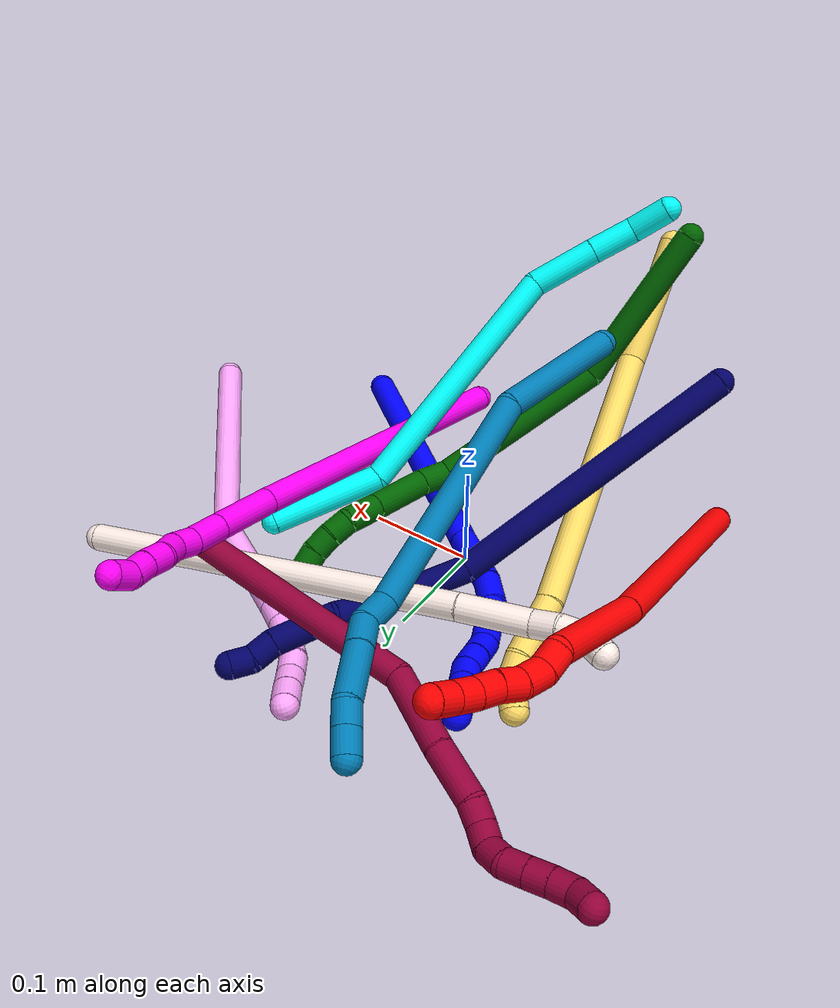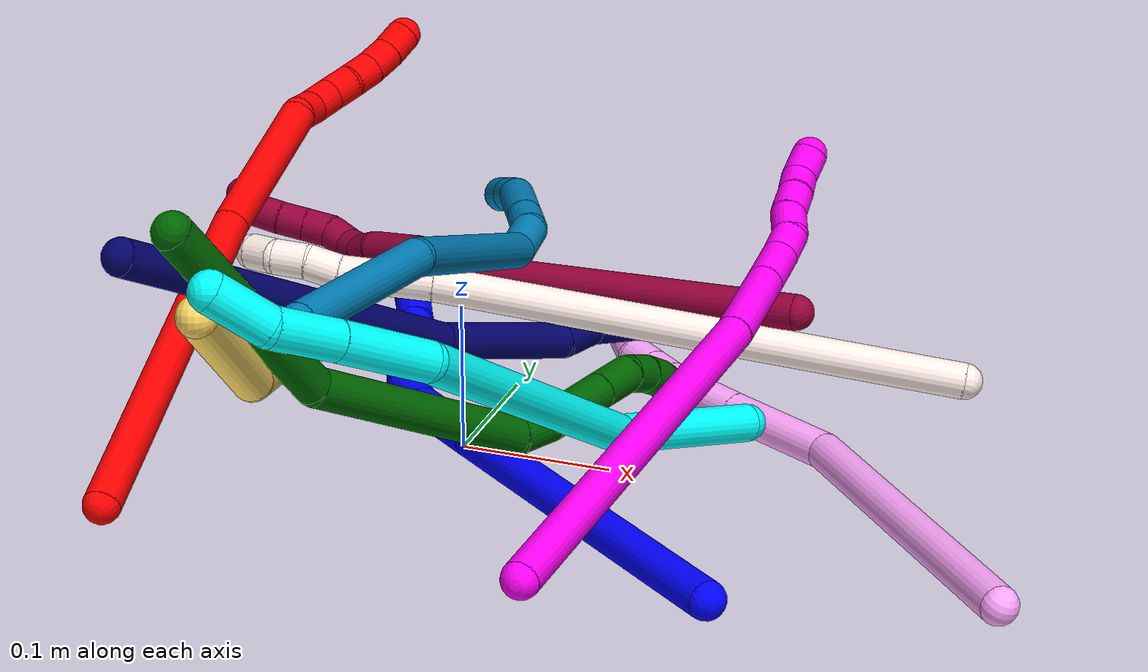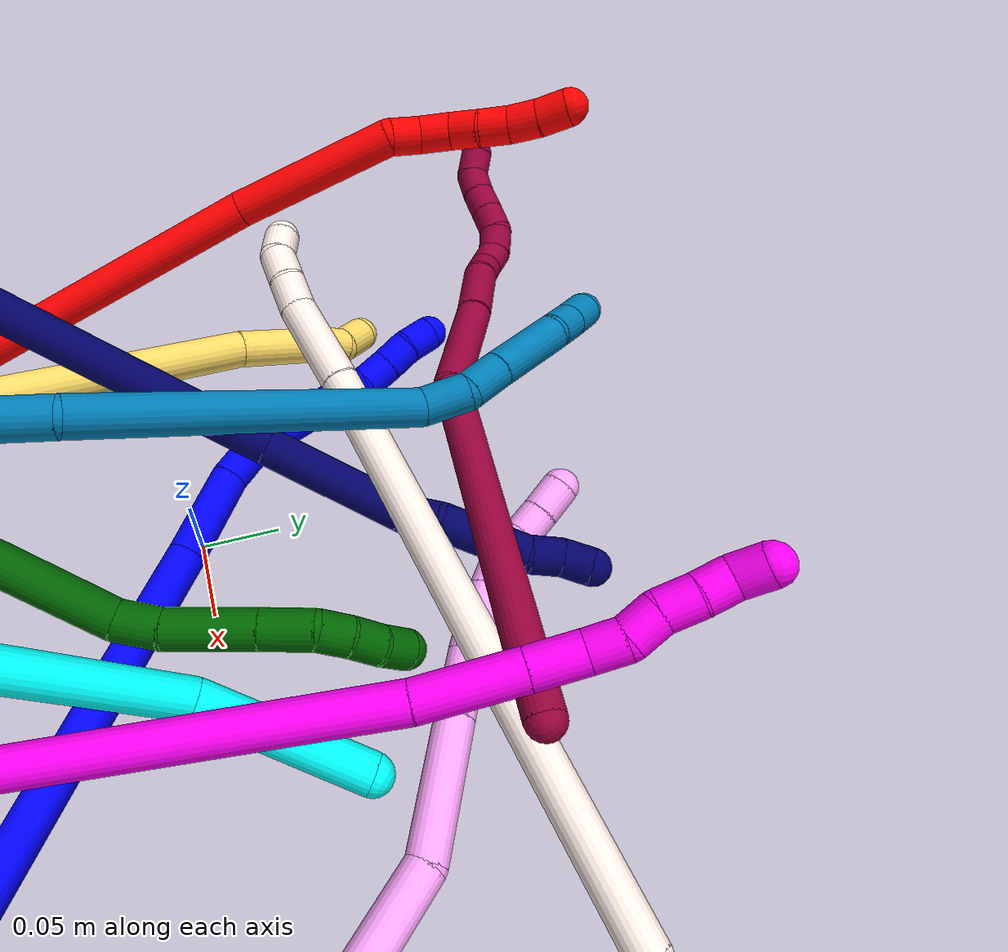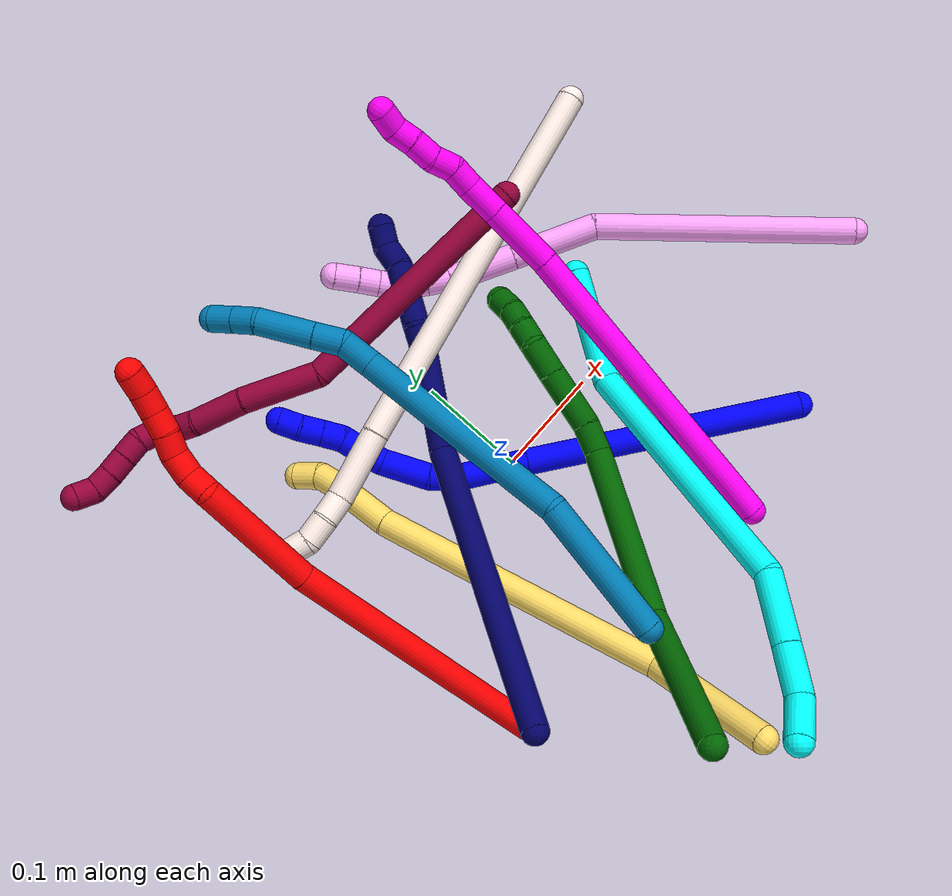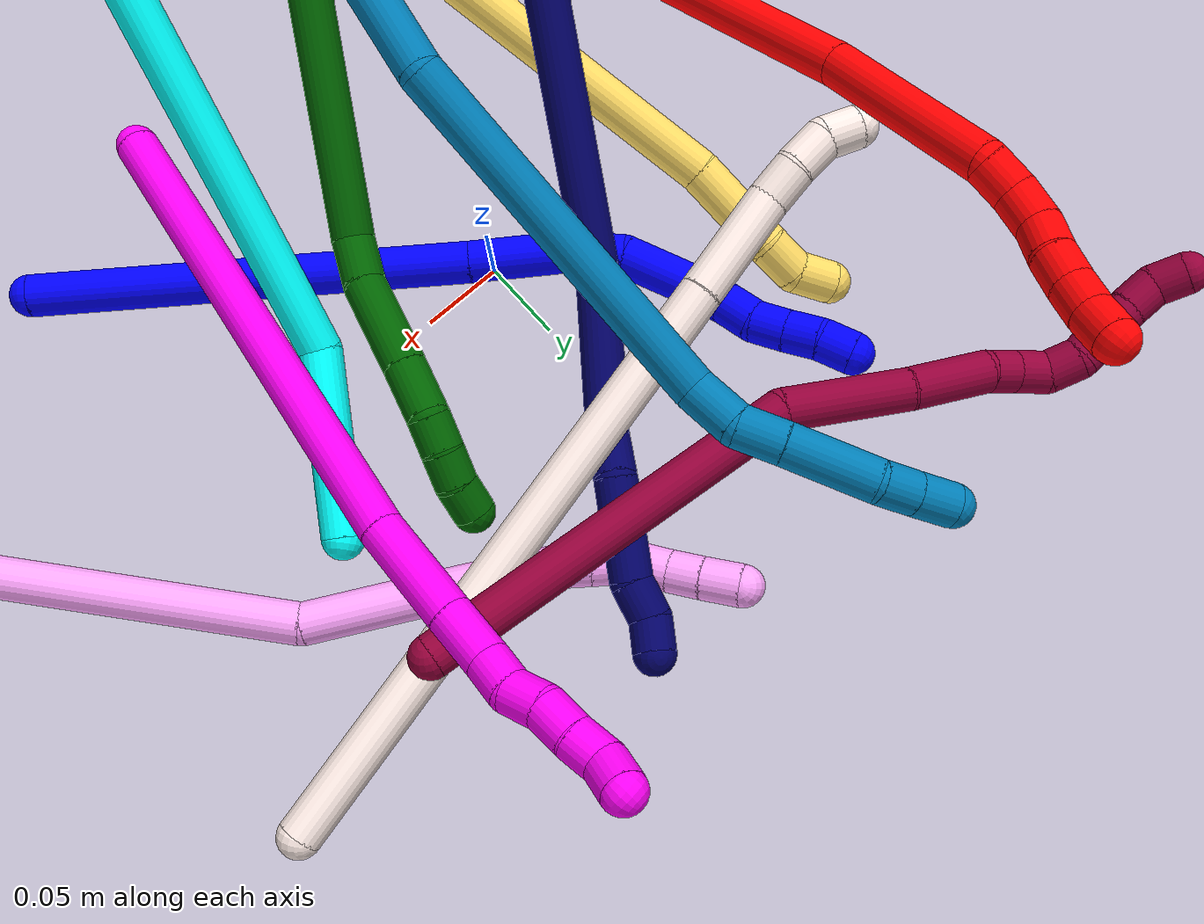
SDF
<sdf version="1.7">
 <world name="default">
  <plugin name="TubeGeneratorPlugin" filename="libtube_generator_plugin.so"/>
  <model name="photoneo_s_sensor">
   <static>1</static>
   <pose>0 0 2 1.57079 1.57079 3.14159</pose>
   <link name="link">
    <inertial><mass>0.1</mass></inertial>
    <sensor name="sensor" type="depth">
     <update_rate>30</update_rate>
     <camera>
      <horizontal_fov>1.22</horizontal_fov>
      <image><width>1920</width><height>1200</height><format>B8G8R8</format></image>
      <clip><near>0.1</near><far>4</far></clip>
      <depth_camera><output>points</output></depth_camera>
     </camera>
     <plugin name="camera_plugin" filename="libgazebo_ros_depth_camera.so">
      <baseline>0.2</baseline>
      <alwaysOn>1</alwaysOn>
      <updateRate>0.0</updateRate>
      <cameraName>camera_ir</cameraName>
      <imageTopicName>/camera/color/image_raw</imageTopicName>
      <cameraInfoTopicName>/camera/color/camera_info</cameraInfoTopicName>
      <depthImageTopicName>/camera/depth/image_raw</depthImageTopicName>
      <depthImageCameraInfoTopicName>/camera/depth/camera_info</depthImageCameraInfoTopicName>
      <pointCloudTopicName>/camera/depth/points</pointCloudTopicName>
      <frameName>fr_optical</frameName>
      <pointCloudCutoff>0.1</pointCloudCutoff>
      <pointCloudCutoffMax>2.0</pointCloudCutoffMax>
      <distortionK1>0</distortionK1>
      <distortionK2>0</distortionK2>
      <distortionK3>0</distortionK3>
      <distortionT1>0</distortionT1>
      <distortionT2>0</distortionT2>
      <CxPrime>0</CxPrime>
      <Cx>0</Cx>
      <Cy>0</Cy>
      <focalLength>0</focalLength>
      <hackBaseline>0</hackBaseline>
     </plugin>
    </sensor>
   </link>
  </model>
  <gravity>0 0 -9.8</gravity>
  <magnetic_field>6e-06 2.3e-05 -4.2e-05</magnetic_field>
  <atmosphere type="adiabatic"/>
  <physics name="default_physics" default="0" type="ode">
   <max_step_size>0.003</max_step_size>
   <real_time_factor>1</real_time_factor>
   <real_time_update_rate>1000</real_time_update_rate>
   <max_contacts>10000</max_contacts>
   <ode>
    <solver>
     <type>quick</type>
     <iters>100</iters>
     <sor>1.3</sor>
     <use_dynamic_moi_rescaling>0</use_dynamic_moi_rescaling>
    </solver>
    <constraints>
     <contact_max_correcting_vel>0</contact_max_correcting_vel>
     <contact_surface_layer>0.001</contact_surface_layer>
     <cfm>0</cfm>
     <erp>0.2</erp>
    </constraints>
   </ode>
  </physics>
  <scene><ambient>0.4 0.4 0.4 1</ambient><background>0.7 0.7 0.7 1</background><shadows>0</shadows></scene>
  <audio><device>default</device></audio>
  <spherical_coordinates>
   <surface_model>EARTH_WGS84</surface_model>
   <latitude_deg>0</latitude_deg>
   <longitude_deg>0</longitude_deg>
   <elevation>0</elevation>
   <heading_deg>0</heading_deg>
  </spherical_coordinates>
  <model name="bin">
   <static>1</static>
   <link name="bottom">
    <collision name="collision-bottom">
     <pose>0 0 -0.01 0 -0 0</pose>
     <geometry><box><size>0.8 0.6 0.02</size></box></geometry>
     <surface>
      <friction><ode><mu>100</mu><mu2>100</mu2></ode></friction>
      <contact><collide_bitmask>65535</collide_bitmask></contact>
     </surface>
    </collision>
   </link>
   <link name="west_wall">
    <collision name="collision-west_wall">
     <pose>-0.41 0 0.1 0 -0 0</pose>
     <geometry><box><size>0.02 0.6 0.2</size></box></geometry>
     <surface>
      <friction><ode><mu>100</mu><mu2>100</mu2></ode></friction>
      <contact><collide_bitmask>65535</collide_bitmask></contact>
     </surface>
    </collision>
   </link>
   <link name="east_wall">
    <collision name="collision-east_wall">
     <pose>0.41 0 0.1 0 -0 0</pose>
     <geometry><box><size>0.02 0.6 0.2</size></box></geometry>
     <surface>
      <friction><ode><mu>100</mu><mu2>100</mu2></ode></friction>
      <contact><collide_bitmask>65535</collide_bitmask></contact>
     </surface>
    </collision>
   </link>
   <link name="south_wall">
    <collision name="collision-south_wall">
     <pose>0 -0.31 0.1 0 -0 0</pose>
     <geometry><box><size>0.8 0.02 0.2</size></box></geometry>
     <surface>
      <friction><ode><mu>100</mu><mu2>100</mu2></ode></friction>
      <contact><collide_bitmask>65535</collide_bitmask></contact>
     </surface>
    </collision>
   </link>
   <link name="north_wall">
    <collision name="collision-north_wall">
     <pose>0 0.31 0.1 0 -0 0</pose>
     <geometry><box><size>0.8 0.02 0.2</size></box></geometry>
     <surface>
      <friction><ode><mu>100</mu><mu2>100</mu2></ode></friction>
      <contact><collide_bitmask>65535</collide_bitmask></contact>
     </surface>
    </collision>
   </link>
  </model>
  <model name="1">
   <static>0</static>
   <link name="1">
    <collision name="collision-cylinder-e_1_1_4">
     <pose>-0.104209 0.070821 -0.027122 -1.93653 -0.941698 1.27418</pose>
     <geometry><cylinder><radius>0.0125</radius><length>0.257766</length></cylinder></geometry>
     <surface>
      <friction><ode><mu>1.16</mu><mu2>1.16</mu2><slip1>0</slip1><slip2>0</slip2></ode></friction>
      <contact><ode><kp>1e+06</kp><kd>1</kd><max_vel>0</max_vel><min_depth>0.001</min_depth></ode></contact>
     </surface>
    </collision>
    <visual name="visual-cylinder-e_1_1_4">
     <pose>-0.104209 0.070821 -0.027122 -1.93653 -0.941698 1.27418</pose>
     <geometry><cylinder><radius>0.0125</radius><length>0.257766</length></cylinder></geometry>
     <material><ambient>0 0 1 1</ambient></material>
    </visual>
    <collision name="collision-cylinder-e_2_4_5">
     <pose>-0.233343 0.157552 -0.060925 -1.9684 -0.965217 1.33512</pose>
     <geometry><cylinder><radius>0.0125</radius><length>0.060629</length></cylinder></geometry>
     <surface>
      <friction><ode><mu>1.16</mu><mu2>1.16</mu2><slip1>0</slip1><slip2>0</slip2></ode></friction>
      <contact><ode><kp>1e+06</kp><kd>1</kd><max_vel>0</max_vel><min_depth>0.001</min_depth></ode></contact>
     </surface>
    </collision>
    <visual name="visual-cylinder-e_2_4_5">
     <pose>-0.233343 0.157552 -0.060925 -1.9684 -0.965217 1.33512</pose>
     <geometry><cylinder><radius>0.0125</radius><length>0.060629</length></cylinder></geometry>
     <material><ambient>0 0 1 1</ambient></material>
    </visual>
    <collision name="collision-cylinder-e_3_5_6">
     <pose>-0.271185 0.182482 -0.067927 -1.60625 -0.960974 0.990339</pose>
     <geometry><cylinder><radius>0.0125</radius><length>0.031519</length></cylinder></geometry>
     <surface>
      <friction><ode><mu>1.16</mu><mu2>1.16</mu2><slip1>0</slip1><slip2>0</slip2></ode></friction>
      <contact><ode><kp>1e+06</kp><kd>1</kd><max_vel>0</max_vel><min_depth>0.001</min_depth></ode></contact>
     </surface>
    </collision>
    <visual name="visual-cylinder-e_3_5_6">
     <pose>-0.271185 0.182482 -0.067927 -1.60625 -0.960974 0.990339</pose>
     <geometry><cylinder><radius>0.0125</radius><length>0.031519</length></cylinder></geometry>
     <material><ambient>0 0 1 1</ambient></material>
    </visual>
    <collision name="collision-cylinder-e_4_6_7">
     <pose>-0.300051 0.20736 -0.062082 -1.2 -0.753032 0.528343</pose>
     <geometry><cylinder><radius>0.0125</radius><length>0.046637</length></cylinder></geometry>
     <surface>
      <friction><ode><mu>1.16</mu><mu2>1.16</mu2><slip1>0</slip1><slip2>0</slip2></ode></friction>
      <contact><ode><kp>1e+06</kp><kd>1</kd><max_vel>0</max_vel><min_depth>0.001</min_depth></ode></contact>
     </surface>
    </collision>
    <visual name="visual-cylinder-e_4_6_7">
     <pose>-0.300051 0.20736 -0.062082 -1.2 -0.753032 0.528343</pose>
     <geometry><cylinder><radius>0.0125</radius><length>0.046637</length></cylinder></geometry>
     <material><ambient>0 0 1 1</ambient></material>
    </visual>
    <collision name="collision-cylinder-e_5_7_8">
     <pose>-0.324289 0.227691 -0.050191 -0.663258 -0.8512 0.309689</pose>
     <geometry><cylinder><radius>0.0125</radius><length>0.02205</length></cylinder></geometry>
     <surface>
      <friction><ode><mu>1.16</mu><mu2>1.16</mu2><slip1>0</slip1><slip2>0</slip2></ode></friction>
      <contact><ode><kp>1e+06</kp><kd>1</kd><max_vel>0</max_vel><min_depth>0.001</min_depth></ode></contact>
     </surface>
    </collision>
    <visual name="visual-cylinder-e_5_7_8">
     <pose>-0.324289 0.227691 -0.050191 -0.663258 -0.8512 0.309689</pose>
     <geometry><cylinder><radius>0.0125</radius><length>0.02205</length></cylinder></geometry>
     <material><ambient>0 0 1 1</ambient></material>
    </visual>
    <collision name="collision-cylinder-e_6_8_9">
     <pose>-0.339784 0.237047 -0.038856 -0.716135 -0.769476 0.300751</pose>
     <geometry><cylinder><radius>0.0125</radius><length>0.020705</length></cylinder></geometry>
     <surface>
      <friction><ode><mu>1.16</mu><mu2>1.16</mu2><slip1>0</slip1><slip2>0</slip2></ode></friction>
      <contact><ode><kp>1e+06</kp><kd>1</kd><max_vel>0</max_vel><min_depth>0.001</min_depth></ode></contact>
     </surface>
    </collision>
    <visual name="visual-cylinder-e_6_8_9">
     <pose>-0.339784 0.237047 -0.038856 -0.716135 -0.769476 0.300751</pose>
     <geometry><cylinder><radius>0.0125</radius><length>0.020705</length></cylinder></geometry>
     <material><ambient>0 0 1 1</ambient></material>
    </visual>
    <collision name="collision-cylinder-e_7_9_10">
     <pose>-0.355436 0.246926 -0.030358 -1.04676 -0.971448 0.591405</pose>
     <geometry><cylinder><radius>0.0125</radius><length>0.020467</length></cylinder></geometry>
     <surface>
      <friction><ode><mu>1.16</mu><mu2>1.16</mu2><slip1>0</slip1><slip2>0</slip2></ode></friction>
      <contact><ode><kp>1e+06</kp><kd>1</kd><max_vel>0</max_vel><min_depth>0.001</min_depth></ode></contact>
     </surface>
    </collision>
    <visual name="visual-cylinder-e_7_9_10">
     <pose>-0.355436 0.246926 -0.030358 -1.04676 -0.971448 0.591405</pose>
     <geometry><cylinder><radius>0.0125</radius><length>0.020467</length></cylinder></geometry>
     <material><ambient>0 0 1 1</ambient></material>
    </visual>
    <collision name="collision-cylinder-e_8_10_11">
     <pose>-0.372512 0.256433 -0.024746 -1.02741 -1.02261 0.613194</pose>
     <geometry><cylinder><radius>0.0125</radius><length>0.020215</length></cylinder></geometry>
     <surface>
      <friction><ode><mu>1.16</mu><mu2>1.16</mu2><slip1>0</slip1><slip2>0</slip2></ode></friction>
      <contact><ode><kp>1e+06</kp><kd>1</kd><max_vel>0</max_vel><min_depth>0.001</min_depth></ode></contact>
     </surface>
    </collision>
    <visual name="visual-cylinder-e_8_10_11">
     <pose>-0.372512 0.256433 -0.024746 -1.02741 -1.02261 0.613194</pose>
     <geometry><cylinder><radius>0.0125</radius><length>0.020215</length></cylinder></geometry>
     <material><ambient>0 0 1 1</ambient></material>
    </visual>
    <collision name="collision-cylinder-e_9_11_2">
     <pose>-0.388389 0.26705 -0.018824 -1.08835 -0.810516 0.507986</pose>
     <geometry><cylinder><radius>0.0125</radius><length>0.020012</length></cylinder></geometry>
     <surface>
      <friction><ode><mu>1.16</mu><mu2>1.16</mu2><slip1>0</slip1><slip2>0</slip2></ode></friction>
      <contact><ode><kp>1e+06</kp><kd>1</kd><max_vel>0</max_vel><min_depth>0.001</min_depth></ode></contact>
     </surface>
    </collision>
    <visual name="visual-cylinder-e_9_11_2">
     <pose>-0.388389 0.26705 -0.018824 -1.08835 -0.810516 0.507986</pose>
     <geometry><cylinder><radius>0.0125</radius><length>0.020012</length></cylinder></geometry>
     <material><ambient>0 0 1 1</ambient></material>
    </visual>
    <collision name="collision-sphere-2">
     <pose>-0.39564 0.273158 -0.015625 0 -0 0</pose>
     <geometry><sphere><radius>0.0125</radius></sphere></geometry>
     <surface>
      <friction><ode><mu>1.16</mu><mu2>1.16</mu2><slip1>0</slip1><slip2>0</slip2></ode></friction>
      <contact><ode><kp>1e+06</kp><kd>1</kd><max_vel>0</max_vel><min_depth>0.001</min_depth></ode></contact>
     </surface>
    </collision>
    <visual name="visual-sphere-2">
     <pose>-0.39564 0.273158 -0.015625 0 -0 0</pose>
     <geometry><sphere><radius>0.0125</radius></sphere></geometry>
     <material><ambient>0 0 1 1</ambient></material>
    </visual>
    <collision name="collision-sphere-11">
     <pose>-0.381138 0.260942 -0.022023 0 -0 0</pose>
     <geometry><sphere><radius>0.0125</radius></sphere></geometry>
     <surface>
      <friction><ode><mu>1.16</mu><mu2>1.16</mu2><slip1>0</slip1><slip2>0</slip2></ode></friction>
      <contact><ode><kp>1e+06</kp><kd>1</kd><max_vel>0</max_vel><min_depth>0.001</min_depth></ode></contact>
     </surface>
    </collision>
    <visual name="visual-sphere-11">
     <pose>-0.381138 0.260942 -0.022023 0 -0 0</pose>
     <geometry><sphere><radius>0.0125</radius></sphere></geometry>
     <material><ambient>0 0 1 1</ambient></material>
    </visual>
    <collision name="collision-sphere-10">
     <pose>-0.363886 0.251924 -0.02747 0 -0 0</pose>
     <geometry><sphere><radius>0.0125</radius></sphere></geometry>
     <surface>
      <friction><ode><mu>1.16</mu><mu2>1.16</mu2><slip1>0</slip1><slip2>0</slip2></ode></friction>
      <contact><ode><kp>1e+06</kp><kd>1</kd><max_vel>0</max_vel><min_depth>0.001</min_depth></ode></contact>
     </surface>
    </collision>
    <visual name="visual-sphere-10">
     <pose>-0.363886 0.251924 -0.02747 0 -0 0</pose>
     <geometry><sphere><radius>0.0125</radius></sphere></geometry>
     <material><ambient>0 0 1 1</ambient></material>
    </visual>
    <collision name="collision-sphere-9">
     <pose>-0.346986 0.241928 -0.033247 0 -0 0</pose>
     <geometry><sphere><radius>0.0125</radius></sphere></geometry>
     <surface>
      <friction><ode><mu>1.16</mu><mu2>1.16</mu2><slip1>0</slip1><slip2>0</slip2></ode></friction>
      <contact><ode><kp>1e+06</kp><kd>1</kd><max_vel>0</max_vel><min_depth>0.001</min_depth></ode></contact>
     </surface>
    </collision>
    <visual name="visual-sphere-9">
     <pose>-0.346986 0.241928 -0.033247 0 -0 0</pose>
     <geometry><sphere><radius>0.0125</radius></sphere></geometry>
     <material><ambient>0 0 1 1</ambient></material>
    </visual>
    <collision name="collision-sphere-4">
     <pose>-0.208419 0.141642 -0.054244 0 -0 0</pose>
     <geometry><sphere><radius>0.0125</radius></sphere></geometry>
     <surface>
      <friction><ode><mu>1.16</mu><mu2>1.16</mu2><slip1>0</slip1><slip2>0</slip2></ode></friction>
      <contact><ode><kp>1e+06</kp><kd>1</kd><max_vel>0</max_vel><min_depth>0.001</min_depth></ode></contact>
     </surface>
    </collision>
    <visual name="visual-sphere-4">
     <pose>-0.208419 0.141642 -0.054244 0 -0 0</pose>
     <geometry><sphere><radius>0.0125</radius></sphere></geometry>
     <material><ambient>0 0 1 1</ambient></material>
    </visual>
    <collision name="collision-sphere-1">
     <geometry><sphere><radius>0.0125</radius></sphere></geometry>
     <surface>
      <friction><ode><mu>1.16</mu><mu2>1.16</mu2><slip1>0</slip1><slip2>0</slip2></ode></friction>
      <contact><ode><kp>1e+06</kp><kd>1</kd><max_vel>0</max_vel><min_depth>0.001</min_depth></ode></contact>
     </surface>
    </collision>
    <visual name="visual-sphere-1">
     <geometry><sphere><radius>0.0125</radius></sphere></geometry>
     <material><ambient>0 0 1 1</ambient></material>
    </visual>
    <collision name="collision-sphere-8">
     <pose>-0.332581 0.232165 -0.044465 0 -0 0</pose>
     <geometry><sphere><radius>0.0125</radius></sphere></geometry>
     <surface>
      <friction><ode><mu>1.16</mu><mu2>1.16</mu2><slip1>0</slip1><slip2>0</slip2></ode></friction>
      <contact><ode><kp>1e+06</kp><kd>1</kd><max_vel>0</max_vel><min_depth>0.001</min_depth></ode></contact>
     </surface>
    </collision>
    <visual name="visual-sphere-8">
     <pose>-0.332581 0.232165 -0.044465 0 -0 0</pose>
     <geometry><sphere><radius>0.0125</radius></sphere></geometry>
     <material><ambient>0 0 1 1</ambient></material>
    </visual>
    <collision name="collision-sphere-5">
     <pose>-0.258267 0.173462 -0.067607 0 -0 0</pose>
     <geometry><sphere><radius>0.0125</radius></sphere></geometry>
     <surface>
      <friction><ode><mu>1.16</mu><mu2>1.16</mu2><slip1>0</slip1><slip2>0</slip2></ode></friction>
      <contact><ode><kp>1e+06</kp><kd>1</kd><max_vel>0</max_vel><min_depth>0.001</min_depth></ode></contact>
     </surface>
    </collision>
    <visual name="visual-sphere-5">
     <pose>-0.258267 0.173462 -0.067607 0 -0 0</pose>
     <geometry><sphere><radius>0.0125</radius></sphere></geometry>
     <material><ambient>0 0 1 1</ambient></material>
    </visual>
    <collision name="collision-sphere-6">
     <pose>-0.284104 0.191503 -0.068247 0 -0 0</pose>
     <geometry><sphere><radius>0.0125</radius></sphere></geometry>
     <surface>
      <friction><ode><mu>1.16</mu><mu2>1.16</mu2><slip1>0</slip1><slip2>0</slip2></ode></friction>
      <contact><ode><kp>1e+06</kp><kd>1</kd><max_vel>0</max_vel><min_depth>0.001</min_depth></ode></contact>
     </surface>
    </collision>
    <visual name="visual-sphere-6">
     <pose>-0.284104 0.191503 -0.068247 0 -0 0</pose>
     <geometry><sphere><radius>0.0125</radius></sphere></geometry>
     <material><ambient>0 0 1 1</ambient></material>
    </visual>
    <collision name="collision-sphere-7">
     <pose>-0.315997 0.223217 -0.055917 0 -0 0</pose>
     <geometry><sphere><radius>0.0125</radius></sphere></geometry>
     <surface>
      <friction><ode><mu>1.16</mu><mu2>1.16</mu2><slip1>0</slip1><slip2>0</slip2></ode></friction>
      <contact><ode><kp>1e+06</kp><kd>1</kd><max_vel>0</max_vel><min_depth>0.001</min_depth></ode></contact>
     </surface>
    </collision>
    <visual name="visual-sphere-7">
     <pose>-0.315997 0.223217 -0.055917 0 -0 0</pose>
     <geometry><sphere><radius>0.0125</radius></sphere></geometry>
     <material><ambient>0 0 1 1</ambient></material>
    </visual>
    <inertial>
     <pose>-0.200626 0.13748 -0.038262 0 -0 0</pose>
     <mass>0.5</mass>
     <inertia>
      <ixx>0.001059</ixx>
      <ixy>0</ixy>
      <ixz>0</ixz>
      <iyy>0.001766</iyy>
      <iyz>0</iyz>
      <izz>0.000381</izz>
     </inertia>
    </inertial>
   </link>
   <pose>0.216163 -0.164299 0.012764 -1.23056 0.624036 -0.656018</pose>
  </model>
  <model name="2">
   <static>0</static>
   <link name="2">
    <collision name="collision-cylinder-e_1_1_4">
     <pose>-0.014871 0.023188 0.128229 -0.1789 -0.113627 0.010202</pose>
     <geometry><cylinder><radius>0.0125</radius><length>0.262309</length></cylinder></geometry>
     <surface>
      <friction><ode><mu>1.16</mu><mu2>1.16</mu2><slip1>0</slip1><slip2>0</slip2></ode></friction>
      <contact><ode><kp>1e+06</kp><kd>1</kd><max_vel>0</max_vel><min_depth>0.001</min_depth></ode></contact>
     </surface>
    </collision>
    <visual name="visual-cylinder-e_1_1_4">
     <pose>-0.014871 0.023188 0.128229 -0.1789 -0.113627 0.010202</pose>
     <geometry><cylinder><radius>0.0125</radius><length>0.262309</length></cylinder></geometry>
     <material><ambient>1 0 0 1</ambient></material>
    </visual>
    <collision name="collision-cylinder-e_2_4_5">
     <pose>-0.042029 0.051682 0.311785 -0.095614 -0.217575 0.010451</pose>
     <geometry><cylinder><radius>0.0125</radius><length>0.113847</length></cylinder></geometry>
     <surface>
      <friction><ode><mu>1.16</mu><mu2>1.16</mu2><slip1>0</slip1><slip2>0</slip2></ode></friction>
      <contact><ode><kp>1e+06</kp><kd>1</kd><max_vel>0</max_vel><min_depth>0.001</min_depth></ode></contact>
     </surface>
    </collision>
    <visual name="visual-cylinder-e_2_4_5">
     <pose>-0.042029 0.051682 0.311785 -0.095614 -0.217575 0.010451</pose>
     <geometry><cylinder><radius>0.0125</radius><length>0.113847</length></cylinder></geometry>
     <material><ambient>1 0 0 1</ambient></material>
    </visual>
    <collision name="collision-cylinder-e_3_5_6">
     <pose>-0.052069 0.055121 0.377386 0.179868 0.212081 0.019196</pose>
     <geometry><cylinder><radius>0.0125</radius><length>0.021361</length></cylinder></geometry>
     <surface>
      <friction><ode><mu>1.16</mu><mu2>1.16</mu2><slip1>0</slip1><slip2>0</slip2></ode></friction>
      <contact><ode><kp>1e+06</kp><kd>1</kd><max_vel>0</max_vel><min_depth>0.001</min_depth></ode></contact>
     </surface>
    </collision>
    <visual name="visual-cylinder-e_3_5_6">
     <pose>-0.052069 0.055121 0.377386 0.179868 0.212081 0.019196</pose>
     <geometry><cylinder><radius>0.0125</radius><length>0.021361</length></cylinder></geometry>
     <material><ambient>1 0 0 1</ambient></material>
    </visual>
    <collision name="collision-cylinder-e_4_6_7">
     <pose>-0.051446 0.050841 0.398464 0.219578 -0.145811 -0.016101</pose>
     <geometry><cylinder><radius>0.0125</radius><length>0.022379</length></cylinder></geometry>
     <surface>
      <friction><ode><mu>1.16</mu><mu2>1.16</mu2><slip1>0</slip1><slip2>0</slip2></ode></friction>
      <contact><ode><kp>1e+06</kp><kd>1</kd><max_vel>0</max_vel><min_depth>0.001</min_depth></ode></contact>
     </surface>
    </collision>
    <visual name="visual-cylinder-e_4_6_7">
     <pose>-0.051446 0.050841 0.398464 0.219578 -0.145811 -0.016101</pose>
     <geometry><cylinder><radius>0.0125</radius><length>0.022379</length></cylinder></geometry>
     <material><ambient>1 0 0 1</ambient></material>
    </visual>
    <collision name="collision-cylinder-e_5_7_8">
     <pose>-0.057433 0.045515 0.417806 0.32903 -0.4503 -0.076009</pose>
     <geometry><cylinder><radius>0.0125</radius><length>0.020041</length></cylinder></geometry>
     <surface>
      <friction><ode><mu>1.16</mu><mu2>1.16</mu2><slip1>0</slip1><slip2>0</slip2></ode></friction>
      <contact><ode><kp>1e+06</kp><kd>1</kd><max_vel>0</max_vel><min_depth>0.001</min_depth></ode></contact>
     </surface>
    </collision>
    <visual name="visual-cylinder-e_5_7_8">
     <pose>-0.057433 0.045515 0.417806 0.32903 -0.4503 -0.076009</pose>
     <geometry><cylinder><radius>0.0125</radius><length>0.020041</length></cylinder></geometry>
     <material><ambient>1 0 0 1</ambient></material>
    </visual>
    <collision name="collision-cylinder-e_6_8_9">
     <pose>-0.064625 0.040121 0.43563 0.260816 -0.286375 -0.037813</pose>
     <geometry><cylinder><radius>0.0125</radius><length>0.020039</length></cylinder></geometry>
     <surface>
      <friction><ode><mu>1.16</mu><mu2>1.16</mu2><slip1>0</slip1><slip2>0</slip2></ode></friction>
      <contact><ode><kp>1e+06</kp><kd>1</kd><max_vel>0</max_vel><min_depth>0.001</min_depth></ode></contact>
     </surface>
    </collision>
    <visual name="visual-cylinder-e_6_8_9">
     <pose>-0.064625 0.040121 0.43563 0.260816 -0.286375 -0.037813</pose>
     <geometry><cylinder><radius>0.0125</radius><length>0.020039</length></cylinder></geometry>
     <material><ambient>1 0 0 1</ambient></material>
    </visual>
    <collision name="collision-cylinder-e_7_9_10">
     <pose>-0.071341 0.036028 0.453989 0.176165 -0.399078 -0.035714</pose>
     <geometry><cylinder><radius>0.0125</radius><length>0.020003</length></cylinder></geometry>
     <surface>
      <friction><ode><mu>1.16</mu><mu2>1.16</mu2><slip1>0</slip1><slip2>0</slip2></ode></friction>
      <contact><ode><kp>1e+06</kp><kd>1</kd><max_vel>0</max_vel><min_depth>0.001</min_depth></ode></contact>
     </surface>
    </collision>
    <visual name="visual-cylinder-e_7_9_10">
     <pose>-0.071341 0.036028 0.453989 0.176165 -0.399078 -0.035714</pose>
     <geometry><cylinder><radius>0.0125</radius><length>0.020003</length></cylinder></geometry>
     <material><ambient>1 0 0 1</ambient></material>
    </visual>
    <collision name="collision-cylinder-e_8_10_2">
     <pose>-0.07951 0.033905 0.472096 0.056083 -0.442058 -0.012605</pose>
     <geometry><cylinder><radius>0.0125</radius><length>0.020021</length></cylinder></geometry>
     <surface>
      <friction><ode><mu>1.16</mu><mu2>1.16</mu2><slip1>0</slip1><slip2>0</slip2></ode></friction>
      <contact><ode><kp>1e+06</kp><kd>1</kd><max_vel>0</max_vel><min_depth>0.001</min_depth></ode></contact>
     </surface>
    </collision>
    <visual name="visual-cylinder-e_8_10_2">
     <pose>-0.07951 0.033905 0.472096 0.056083 -0.442058 -0.012605</pose>
     <geometry><cylinder><radius>0.0125</radius><length>0.020021</length></cylinder></geometry>
     <material><ambient>1 0 0 1</ambient></material>
    </visual>
    <collision name="collision-sphere-2">
     <pose>-0.083793 0.033398 0.481131 0 -0 0</pose>
     <geometry><sphere><radius>0.0125</radius></sphere></geometry>
     <surface>
      <friction><ode><mu>1.16</mu><mu2>1.16</mu2><slip1>0</slip1><slip2>0</slip2></ode></friction>
      <contact><ode><kp>1e+06</kp><kd>1</kd><max_vel>0</max_vel><min_depth>0.001</min_depth></ode></contact>
     </surface>
    </collision>
    <visual name="visual-sphere-2">
     <pose>-0.083793 0.033398 0.481131 0 -0 0</pose>
     <geometry><sphere><radius>0.0125</radius></sphere></geometry>
     <material><ambient>1 0 0 1</ambient></material>
    </visual>
    <collision name="collision-sphere-10">
     <pose>-0.075227 0.034413 0.463062 0 -0 0</pose>
     <geometry><sphere><radius>0.0125</radius></sphere></geometry>
     <surface>
      <friction><ode><mu>1.16</mu><mu2>1.16</mu2><slip1>0</slip1><slip2>0</slip2></ode></friction>
      <contact><ode><kp>1e+06</kp><kd>1</kd><max_vel>0</max_vel><min_depth>0.001</min_depth></ode></contact>
     </surface>
    </collision>
    <visual name="visual-sphere-10">
     <pose>-0.075227 0.034413 0.463062 0 -0 0</pose>
     <geometry><sphere><radius>0.0125</radius></sphere></geometry>
     <material><ambient>1 0 0 1</ambient></material>
    </visual>
    <collision name="collision-sphere-9">
     <pose>-0.067455 0.037643 0.444916 0 -0 0</pose>
     <geometry><sphere><radius>0.0125</radius></sphere></geometry>
     <surface>
      <friction><ode><mu>1.16</mu><mu2>1.16</mu2><slip1>0</slip1><slip2>0</slip2></ode></friction>
      <contact><ode><kp>1e+06</kp><kd>1</kd><max_vel>0</max_vel><min_depth>0.001</min_depth></ode></contact>
     </surface>
    </collision>
    <visual name="visual-sphere-9">
     <pose>-0.067455 0.037643 0.444916 0 -0 0</pose>
     <geometry><sphere><radius>0.0125</radius></sphere></geometry>
     <material><ambient>1 0 0 1</ambient></material>
    </visual>
    <collision name="collision-sphere-4">
     <pose>-0.029741 0.046376 0.256458 0 -0 0</pose>
     <geometry><sphere><radius>0.0125</radius></sphere></geometry>
     <surface>
      <friction><ode><mu>1.16</mu><mu2>1.16</mu2><slip1>0</slip1><slip2>0</slip2></ode></friction>
      <contact><ode><kp>1e+06</kp><kd>1</kd><max_vel>0</max_vel><min_depth>0.001</min_depth></ode></contact>
     </surface>
    </collision>
    <visual name="visual-sphere-4">
     <pose>-0.029741 0.046376 0.256458 0 -0 0</pose>
     <geometry><sphere><radius>0.0125</radius></sphere></geometry>
     <material><ambient>1 0 0 1</ambient></material>
    </visual>
    <collision name="collision-sphere-1">
     <geometry><sphere><radius>0.0125</radius></sphere></geometry>
     <surface>
      <friction><ode><mu>1.16</mu><mu2>1.16</mu2><slip1>0</slip1><slip2>0</slip2></ode></friction>
      <contact><ode><kp>1e+06</kp><kd>1</kd><max_vel>0</max_vel><min_depth>0.001</min_depth></ode></contact>
     </surface>
    </collision>
    <visual name="visual-sphere-1">
     <geometry><sphere><radius>0.0125</radius></sphere></geometry>
     <material><ambient>1 0 0 1</ambient></material>
    </visual>
    <collision name="collision-sphere-8">
     <pose>-0.061794 0.0426 0.426344 0 -0 0</pose>
     <geometry><sphere><radius>0.0125</radius></sphere></geometry>
     <surface>
      <friction><ode><mu>1.16</mu><mu2>1.16</mu2><slip1>0</slip1><slip2>0</slip2></ode></friction>
      <contact><ode><kp>1e+06</kp><kd>1</kd><max_vel>0</max_vel><min_depth>0.001</min_depth></ode></contact>
     </surface>
    </collision>
    <visual name="visual-sphere-8">
     <pose>-0.061794 0.0426 0.426344 0 -0 0</pose>
     <geometry><sphere><radius>0.0125</radius></sphere></geometry>
     <material><ambient>1 0 0 1</ambient></material>
    </visual>
    <collision name="collision-sphere-5">
     <pose>-0.054317 0.056989 0.367113 0 -0 0</pose>
     <geometry><sphere><radius>0.0125</radius></sphere></geometry>
     <surface>
      <friction><ode><mu>1.16</mu><mu2>1.16</mu2><slip1>0</slip1><slip2>0</slip2></ode></friction>
      <contact><ode><kp>1e+06</kp><kd>1</kd><max_vel>0</max_vel><min_depth>0.001</min_depth></ode></contact>
     </surface>
    </collision>
    <visual name="visual-sphere-5">
     <pose>-0.054317 0.056989 0.367113 0 -0 0</pose>
     <geometry><sphere><radius>0.0125</radius></sphere></geometry>
     <material><ambient>1 0 0 1</ambient></material>
    </visual>
    <collision name="collision-sphere-6">
     <pose>-0.04982 0.053253 0.387659 0 -0 0</pose>
     <geometry><sphere><radius>0.0125</radius></sphere></geometry>
     <surface>
      <friction><ode><mu>1.16</mu><mu2>1.16</mu2><slip1>0</slip1><slip2>0</slip2></ode></friction>
      <contact><ode><kp>1e+06</kp><kd>1</kd><max_vel>0</max_vel><min_depth>0.001</min_depth></ode></contact>
     </surface>
    </collision>
    <visual name="visual-sphere-6">
     <pose>-0.04982 0.053253 0.387659 0 -0 0</pose>
     <geometry><sphere><radius>0.0125</radius></sphere></geometry>
     <material><ambient>1 0 0 1</ambient></material>
    </visual>
    <collision name="collision-sphere-7">
     <pose>-0.053072 0.04843 0.409269 0 -0 0</pose>
     <geometry><sphere><radius>0.0125</radius></sphere></geometry>
     <surface>
      <friction><ode><mu>1.16</mu><mu2>1.16</mu2><slip1>0</slip1><slip2>0</slip2></ode></friction>
      <contact><ode><kp>1e+06</kp><kd>1</kd><max_vel>0</max_vel><min_depth>0.001</min_depth></ode></contact>
     </surface>
    </collision>
    <visual name="visual-sphere-7">
     <pose>-0.053072 0.04843 0.409269 0 -0 0</pose>
     <geometry><sphere><radius>0.0125</radius></sphere></geometry>
     <material><ambient>1 0 0 1</ambient></material>
    </visual>
    <inertial>
     <pose>-0.032828 0.034794 0.243492 0 -0 0</pose>
     <mass>0.5</mass>
     <inertia>
      <ixx>0.001647</ixx>
      <ixy>0</ixy>
      <ixz>0</ixz>
      <iyy>0.001645</iyy>
      <iyz>0</iyz>
      <izz>-3.9e-05</izz>
     </inertia>
    </inertial>
   </link>
   <pose>-0.173604 -0.172957 0.011498 1.30635 0.916984 2.94623</pose>
  </model>
  <model name="3">
   <static>0</static>
   <link name="3">
    <collision name="collision-cylinder-e_1_1_4">
     <pose>-0.009163 -0.01016 0.052049 0.19277 -0.171099 -0.016583</pose>
     <geometry><cylinder><radius>0.0125</radius><length>0.107634</length></cylinder></geometry>
     <surface>
      <friction><ode><mu>1.16</mu><mu2>1.16</mu2><slip1>0</slip1><slip2>0</slip2></ode></friction>
      <contact><ode><kp>1e+06</kp><kd>1</kd><max_vel>0</max_vel><min_depth>0.001</min_depth></ode></contact>
     </surface>
    </collision>
    <visual name="visual-cylinder-e_1_1_4">
     <pose>-0.009163 -0.01016 0.052049 0.19277 -0.171099 -0.016583</pose>
     <geometry><cylinder><radius>0.0125</radius><length>0.107634</length></cylinder></geometry>
     <material><ambient>0.003922 1 0.996078 1</ambient></material>
    </visual>
    <collision name="collision-cylinder-e_2_4_5">
     <pose>-0.051881 -0.09475 0.195556 0.683113 -0.27723 -0.099107</pose>
     <geometry><cylinder><radius>0.0125</radius><length>0.245197</length></cylinder></geometry>
     <surface>
      <friction><ode><mu>1.16</mu><mu2>1.16</mu2><slip1>0</slip1><slip2>0</slip2></ode></friction>
      <contact><ode><kp>1e+06</kp><kd>1</kd><max_vel>0</max_vel><min_depth>0.001</min_depth></ode></contact>
     </surface>
    </collision>
    <visual name="visual-cylinder-e_2_4_5">
     <pose>-0.051881 -0.09475 0.195556 0.683113 -0.27723 -0.099107</pose>
     <geometry><cylinder><radius>0.0125</radius><length>0.245197</length></cylinder></geometry>
     <material><ambient>0.003922 1 0.996078 1</ambient></material>
    </visual>
    <collision name="collision-cylinder-e_3_5_6">
     <pose>-0.085539 -0.18046 0.316908 0.360795 -0.00326 -0.000595</pose>
     <geometry><cylinder><radius>0.0125</radius><length>0.063903</length></cylinder></geometry>
     <surface>
      <friction><ode><mu>1.16</mu><mu2>1.16</mu2><slip1>0</slip1><slip2>0</slip2></ode></friction>
      <contact><ode><kp>1e+06</kp><kd>1</kd><max_vel>0</max_vel><min_depth>0.001</min_depth></ode></contact>
     </surface>
    </collision>
    <visual name="visual-cylinder-e_3_5_6">
     <pose>-0.085539 -0.18046 0.316908 0.360795 -0.00326 -0.000595</pose>
     <geometry><cylinder><radius>0.0125</radius><length>0.063903</length></cylinder></geometry>
     <material><ambient>0.003922 1 0.996078 1</ambient></material>
    </visual>
    <collision name="collision-cylinder-e_4_6_7">
     <pose>-0.08587 -0.198993 0.367672 0.334506 -0.010249 -0.00173</pose>
     <geometry><cylinder><radius>0.0125</radius><length>0.04419</length></cylinder></geometry>
     <surface>
      <friction><ode><mu>1.16</mu><mu2>1.16</mu2><slip1>0</slip1><slip2>0</slip2></ode></friction>
      <contact><ode><kp>1e+06</kp><kd>1</kd><max_vel>0</max_vel><min_depth>0.001</min_depth></ode></contact>
     </surface>
    </collision>
    <visual name="visual-cylinder-e_4_6_7">
     <pose>-0.08587 -0.198993 0.367672 0.334506 -0.010249 -0.00173</pose>
     <geometry><cylinder><radius>0.0125</radius><length>0.04419</length></cylinder></geometry>
     <material><ambient>0.003922 1 0.996078 1</ambient></material>
    </visual>
    <collision name="collision-cylinder-e_5_7_2">
     <pose>-0.079402 -0.2144 0.404986 0.46028 0.349691 0.082727</pose>
     <geometry><cylinder><radius>0.0125</radius><length>0.039076</length></cylinder></geometry>
     <surface>
      <friction><ode><mu>1.16</mu><mu2>1.16</mu2><slip1>0</slip1><slip2>0</slip2></ode></friction>
      <contact><ode><kp>1e+06</kp><kd>1</kd><max_vel>0</max_vel><min_depth>0.001</min_depth></ode></contact>
     </surface>
    </collision>
    <visual name="visual-cylinder-e_5_7_2">
     <pose>-0.079402 -0.2144 0.404986 0.46028 0.349691 0.082727</pose>
     <geometry><cylinder><radius>0.0125</radius><length>0.039076</length></cylinder></geometry>
     <material><ambient>0.003922 1 0.996078 1</ambient></material>
    </visual>
    <collision name="collision-sphere-2">
     <pose>-0.072709 -0.222553 0.421431 0 -0 0</pose>
     <geometry><sphere><radius>0.0125</radius></sphere></geometry>
     <surface>
      <friction><ode><mu>1.16</mu><mu2>1.16</mu2><slip1>0</slip1><slip2>0</slip2></ode></friction>
      <contact><ode><kp>1e+06</kp><kd>1</kd><max_vel>0</max_vel><min_depth>0.001</min_depth></ode></contact>
     </surface>
    </collision>
    <visual name="visual-sphere-2">
     <pose>-0.072709 -0.222553 0.421431 0 -0 0</pose>
     <geometry><sphere><radius>0.0125</radius></sphere></geometry>
     <material><ambient>0.003922 1 0.996078 1</ambient></material>
    </visual>
    <collision name="collision-sphere-7">
     <pose>-0.086096 -0.206247 0.388541 0 -0 0</pose>
     <geometry><sphere><radius>0.0125</radius></sphere></geometry>
     <surface>
      <friction><ode><mu>1.16</mu><mu2>1.16</mu2><slip1>0</slip1><slip2>0</slip2></ode></friction>
      <contact><ode><kp>1e+06</kp><kd>1</kd><max_vel>0</max_vel><min_depth>0.001</min_depth></ode></contact>
     </surface>
    </collision>
    <visual name="visual-sphere-7">
     <pose>-0.086096 -0.206247 0.388541 0 -0 0</pose>
     <geometry><sphere><radius>0.0125</radius></sphere></geometry>
     <material><ambient>0.003922 1 0.996078 1</ambient></material>
    </visual>
    <collision name="collision-sphere-6">
     <pose>-0.085643 -0.191739 0.346802 0 -0 0</pose>
     <geometry><sphere><radius>0.0125</radius></sphere></geometry>
     <surface>
      <friction><ode><mu>1.16</mu><mu2>1.16</mu2><slip1>0</slip1><slip2>0</slip2></ode></friction>
      <contact><ode><kp>1e+06</kp><kd>1</kd><max_vel>0</max_vel><min_depth>0.001</min_depth></ode></contact>
     </surface>
    </collision>
    <visual name="visual-sphere-6">
     <pose>-0.085643 -0.191739 0.346802 0 -0 0</pose>
     <geometry><sphere><radius>0.0125</radius></sphere></geometry>
     <material><ambient>0.003922 1 0.996078 1</ambient></material>
    </visual>
    <collision name="collision-sphere-5">
     <pose>-0.085435 -0.169181 0.287014 0 -0 0</pose>
     <geometry><sphere><radius>0.0125</radius></sphere></geometry>
     <surface>
      <friction><ode><mu>1.16</mu><mu2>1.16</mu2><slip1>0</slip1><slip2>0</slip2></ode></friction>
      <contact><ode><kp>1e+06</kp><kd>1</kd><max_vel>0</max_vel><min_depth>0.001</min_depth></ode></contact>
     </surface>
    </collision>
    <visual name="visual-sphere-5">
     <pose>-0.085435 -0.169181 0.287014 0 -0 0</pose>
     <geometry><sphere><radius>0.0125</radius></sphere></geometry>
     <material><ambient>0.003922 1 0.996078 1</ambient></material>
    </visual>
    <collision name="collision-sphere-1">
     <geometry><sphere><radius>0.0125</radius></sphere></geometry>
     <surface>
      <friction><ode><mu>1.16</mu><mu2>1.16</mu2><slip1>0</slip1><slip2>0</slip2></ode></friction>
      <contact><ode><kp>1e+06</kp><kd>1</kd><max_vel>0</max_vel><min_depth>0.001</min_depth></ode></contact>
     </surface>
    </collision>
    <visual name="visual-sphere-1">
     <geometry><sphere><radius>0.0125</radius></sphere></geometry>
     <material><ambient>0.003922 1 0.996078 1</ambient></material>
    </visual>
    <collision name="collision-sphere-4">
     <pose>-0.018326 -0.020319 0.104098 0 -0 0</pose>
     <geometry><sphere><radius>0.0125</radius></sphere></geometry>
     <surface>
      <friction><ode><mu>1.16</mu><mu2>1.16</mu2><slip1>0</slip1><slip2>0</slip2></ode></friction>
      <contact><ode><kp>1e+06</kp><kd>1</kd><max_vel>0</max_vel><min_depth>0.001</min_depth></ode></contact>
     </surface>
    </collision>
    <visual name="visual-sphere-4">
     <pose>-0.018326 -0.020319 0.104098 0 -0 0</pose>
     <geometry><sphere><radius>0.0125</radius></sphere></geometry>
     <material><ambient>0.003922 1 0.996078 1</ambient></material>
    </visual>
    <inertial>
     <pose>-0.052142 -0.106059 0.211752 0 -0 0</pose>
     <mass>0.5</mass>
     <inertia>
      <ixx>0.001206</ixx>
      <ixy>0</ixy>
      <ixz>0</ixz>
      <iyy>0.000983</iyy>
      <iyz>0</iyz>
      <izz>0.001174</izz>
     </inertia>
    </inertial>
   </link>
   <pose>0.17103 0.07193 0.012211 -1.4574 -0.384732 2.27096</pose>
  </model>
  <model name="4">
   <static>0</static>
   <link name="4">
    <collision name="collision-cylinder-e_1_1_4">
     <pose>-0.03448 0.107877 -0.043963 -1.95778 -0.287774 0.424515</pose>
     <geometry><cylinder><radius>0.0125</radius><length>0.242975</length></cylinder></geometry>
     <surface>
      <friction><ode><mu>1.16</mu><mu2>1.16</mu2><slip1>0</slip1><slip2>0</slip2></ode></friction>
      <contact><ode><kp>1e+06</kp><kd>1</kd><max_vel>0</max_vel><min_depth>0.001</min_depth></ode></contact>
     </surface>
    </collision>
    <visual name="visual-cylinder-e_1_1_4">
     <pose>-0.03448 0.107877 -0.043963 -1.95778 -0.287774 0.424515</pose>
     <geometry><cylinder><radius>0.0125</radius><length>0.242975</length></cylinder></geometry>
     <material><ambient>1 0.65098 0.996078 1</ambient></material>
    </visual>
    <collision name="collision-cylinder-e_2_4_5">
     <pose>-0.094131 0.24412 -0.104055 -2.08782 -0.657048 1.06006</pose>
     <geometry><cylinder><radius>0.0125</radius><length>0.082418</length></cylinder></geometry>
     <surface>
      <friction><ode><mu>1.16</mu><mu2>1.16</mu2><slip1>0</slip1><slip2>0</slip2></ode></friction>
      <contact><ode><kp>1e+06</kp><kd>1</kd><max_vel>0</max_vel><min_depth>0.001</min_depth></ode></contact>
     </surface>
    </collision>
    <visual name="visual-cylinder-e_2_4_5">
     <pose>-0.094131 0.24412 -0.104055 -2.08782 -0.657048 1.06006</pose>
     <geometry><cylinder><radius>0.0125</radius><length>0.082418</length></cylinder></geometry>
     <material><ambient>1 0.65098 0.996078 1</ambient></material>
    </visual>
    <collision name="collision-cylinder-e_3_5_6">
     <pose>-0.131559 0.286615 -0.127846 -2.06769 -0.651512 1.03226</pose>
     <geometry><cylinder><radius>0.0125</radius><length>0.040431</length></cylinder></geometry>
     <surface>
      <friction><ode><mu>1.16</mu><mu2>1.16</mu2><slip1>0</slip1><slip2>0</slip2></ode></friction>
      <contact><ode><kp>1e+06</kp><kd>1</kd><max_vel>0</max_vel><min_depth>0.001</min_depth></ode></contact>
     </surface>
    </collision>
    <visual name="visual-cylinder-e_3_5_6">
     <pose>-0.131559 0.286615 -0.127846 -2.06769 -0.651512 1.03226</pose>
     <geometry><cylinder><radius>0.0125</radius><length>0.040431</length></cylinder></geometry>
     <material><ambient>1 0.65098 0.996078 1</ambient></material>
    </visual>
    <collision name="collision-cylinder-e_4_6_7">
     <pose>-0.150584 0.309067 -0.139698 -2.03713 -0.628151 0.970285</pose>
     <geometry><cylinder><radius>0.0125</radius><length>0.023029</length></cylinder></geometry>
     <surface>
      <friction><ode><mu>1.16</mu><mu2>1.16</mu2><slip1>0</slip1><slip2>0</slip2></ode></friction>
      <contact><ode><kp>1e+06</kp><kd>1</kd><max_vel>0</max_vel><min_depth>0.001</min_depth></ode></contact>
     </surface>
    </collision>
    <visual name="visual-cylinder-e_4_6_7">
     <pose>-0.150584 0.309067 -0.139698 -2.03713 -0.628151 0.970285</pose>
     <geometry><cylinder><radius>0.0125</radius><length>0.023029</length></cylinder></geometry>
     <material><ambient>1 0.65098 0.996078 1</ambient></material>
    </visual>
    <collision name="collision-cylinder-e_5_7_8">
     <pose>-0.162625 0.326182 -0.147591 -1.96957 -0.504961 0.741374</pose>
     <geometry><cylinder><radius>0.0125</radius><length>0.021804</length></cylinder></geometry>
     <surface>
      <friction><ode><mu>1.16</mu><mu2>1.16</mu2><slip1>0</slip1><slip2>0</slip2></ode></friction>
      <contact><ode><kp>1e+06</kp><kd>1</kd><max_vel>0</max_vel><min_depth>0.001</min_depth></ode></contact>
     </surface>
    </collision>
    <visual name="visual-cylinder-e_5_7_8">
     <pose>-0.162625 0.326182 -0.147591 -1.96957 -0.504961 0.741374</pose>
     <geometry><cylinder><radius>0.0125</radius><length>0.021804</length></cylinder></geometry>
     <material><ambient>1 0.65098 0.996078 1</ambient></material>
    </visual>
    <collision name="collision-cylinder-e_6_8_9">
     <pose>-0.173745 0.34471 -0.1554 -1.96972 -0.505463 0.742181</pose>
     <geometry><cylinder><radius>0.0125</radius><length>0.02415</length></cylinder></geometry>
     <surface>
      <friction><ode><mu>1.16</mu><mu2>1.16</mu2><slip1>0</slip1><slip2>0</slip2></ode></friction>
      <contact><ode><kp>1e+06</kp><kd>1</kd><max_vel>0</max_vel><min_depth>0.001</min_depth></ode></contact>
     </surface>
    </collision>
    <visual name="visual-cylinder-e_6_8_9">
     <pose>-0.173745 0.34471 -0.1554 -1.96972 -0.505463 0.742181</pose>
     <geometry><cylinder><radius>0.0125</radius><length>0.02415</length></cylinder></geometry>
     <material><ambient>1 0.65098 0.996078 1</ambient></material>
    </visual>
    <collision name="collision-cylinder-e_7_9_10">
     <pose>-0.182085 0.364808 -0.161618 -1.77211 -0.23147 0.28285</pose>
     <geometry><cylinder><radius>0.0125</radius><length>0.021733</length></cylinder></geometry>
     <surface>
      <friction><ode><mu>1.16</mu><mu2>1.16</mu2><slip1>0</slip1><slip2>0</slip2></ode></friction>
      <contact><ode><kp>1e+06</kp><kd>1</kd><max_vel>0</max_vel><min_depth>0.001</min_depth></ode></contact>
     </surface>
    </collision>
    <visual name="visual-cylinder-e_7_9_10">
     <pose>-0.182085 0.364808 -0.161618 -1.77211 -0.23147 0.28285</pose>
     <geometry><cylinder><radius>0.0125</radius><length>0.021733</length></cylinder></geometry>
     <material><ambient>1 0.65098 0.996078 1</ambient></material>
    </visual>
    <collision name="collision-cylinder-e_8_10_11">
     <pose>-0.1873 0.384908 -0.164241 -1.62286 -0.272254 0.286618</pose>
     <geometry><cylinder><radius>0.0125</radius><length>0.020246</length></cylinder></geometry>
     <surface>
      <friction><ode><mu>1.16</mu><mu2>1.16</mu2><slip1>0</slip1><slip2>0</slip2></ode></friction>
      <contact><ode><kp>1e+06</kp><kd>1</kd><max_vel>0</max_vel><min_depth>0.001</min_depth></ode></contact>
     </surface>
    </collision>
    <visual name="visual-cylinder-e_8_10_11">
     <pose>-0.1873 0.384908 -0.164241 -1.62286 -0.272254 0.286618</pose>
     <geometry><cylinder><radius>0.0125</radius><length>0.020246</length></cylinder></geometry>
     <material><ambient>1 0.65098 0.996078 1</ambient></material>
    </visual>
    <collision name="collision-cylinder-e_9_11_2">
     <pose>-0.193374 0.405714 -0.165739 -1.66012 -0.2929 0.319858</pose>
     <geometry><cylinder><radius>0.0125</radius><length>0.023214</length></cylinder></geometry>
     <surface>
      <friction><ode><mu>1.16</mu><mu2>1.16</mu2><slip1>0</slip1><slip2>0</slip2></ode></friction>
      <contact><ode><kp>1e+06</kp><kd>1</kd><max_vel>0</max_vel><min_depth>0.001</min_depth></ode></contact>
     </surface>
    </collision>
    <visual name="visual-cylinder-e_9_11_2">
     <pose>-0.193374 0.405714 -0.165739 -1.66012 -0.2929 0.319858</pose>
     <geometry><cylinder><radius>0.0125</radius><length>0.023214</length></cylinder></geometry>
     <material><ambient>1 0.65098 0.996078 1</ambient></material>
    </visual>
    <collision name="collision-sphere-2">
     <pose>-0.196725 0.416782 -0.166731 0 -0 0</pose>
     <geometry><sphere><radius>0.0125</radius></sphere></geometry>
     <surface>
      <friction><ode><mu>1.16</mu><mu2>1.16</mu2><slip1>0</slip1><slip2>0</slip2></ode></friction>
      <contact><ode><kp>1e+06</kp><kd>1</kd><max_vel>0</max_vel><min_depth>0.001</min_depth></ode></contact>
     </surface>
    </collision>
    <visual name="visual-sphere-2">
     <pose>-0.196725 0.416782 -0.166731 0 -0 0</pose>
     <geometry><sphere><radius>0.0125</radius></sphere></geometry>
     <material><ambient>1 0.65098 0.996078 1</ambient></material>
    </visual>
    <collision name="collision-sphere-11">
     <pose>-0.190022 0.394646 -0.164748 0 -0 0</pose>
     <geometry><sphere><radius>0.0125</radius></sphere></geometry>
     <surface>
      <friction><ode><mu>1.16</mu><mu2>1.16</mu2><slip1>0</slip1><slip2>0</slip2></ode></friction>
      <contact><ode><kp>1e+06</kp><kd>1</kd><max_vel>0</max_vel><min_depth>0.001</min_depth></ode></contact>
     </surface>
    </collision>
    <visual name="visual-sphere-11">
     <pose>-0.190022 0.394646 -0.164748 0 -0 0</pose>
     <geometry><sphere><radius>0.0125</radius></sphere></geometry>
     <material><ambient>1 0.65098 0.996078 1</ambient></material>
    </visual>
    <collision name="collision-sphere-10">
     <pose>-0.184578 0.375171 -0.163733 0 -0 0</pose>
     <geometry><sphere><radius>0.0125</radius></sphere></geometry>
     <surface>
      <friction><ode><mu>1.16</mu><mu2>1.16</mu2><slip1>0</slip1><slip2>0</slip2></ode></friction>
      <contact><ode><kp>1e+06</kp><kd>1</kd><max_vel>0</max_vel><min_depth>0.001</min_depth></ode></contact>
     </surface>
    </collision>
    <visual name="visual-sphere-10">
     <pose>-0.184578 0.375171 -0.163733 0 -0 0</pose>
     <geometry><sphere><radius>0.0125</radius></sphere></geometry>
     <material><ambient>1 0.65098 0.996078 1</ambient></material>
    </visual>
    <collision name="collision-sphere-9">
     <pose>-0.179592 0.354446 -0.159504 0 -0 0</pose>
     <geometry><sphere><radius>0.0125</radius></sphere></geometry>
     <surface>
      <friction><ode><mu>1.16</mu><mu2>1.16</mu2><slip1>0</slip1><slip2>0</slip2></ode></friction>
      <contact><ode><kp>1e+06</kp><kd>1</kd><max_vel>0</max_vel><min_depth>0.001</min_depth></ode></contact>
     </surface>
    </collision>
    <visual name="visual-sphere-9">
     <pose>-0.179592 0.354446 -0.159504 0 -0 0</pose>
     <geometry><sphere><radius>0.0125</radius></sphere></geometry>
     <material><ambient>1 0.65098 0.996078 1</ambient></material>
    </visual>
    <collision name="collision-sphere-4">
     <pose>-0.068961 0.215755 -0.087926 0 -0 0</pose>
     <geometry><sphere><radius>0.0125</radius></sphere></geometry>
     <surface>
      <friction><ode><mu>1.16</mu><mu2>1.16</mu2><slip1>0</slip1><slip2>0</slip2></ode></friction>
      <contact><ode><kp>1e+06</kp><kd>1</kd><max_vel>0</max_vel><min_depth>0.001</min_depth></ode></contact>
     </surface>
    </collision>
    <visual name="visual-sphere-4">
     <pose>-0.068961 0.215755 -0.087926 0 -0 0</pose>
     <geometry><sphere><radius>0.0125</radius></sphere></geometry>
     <material><ambient>1 0.65098 0.996078 1</ambient></material>
    </visual>
    <collision name="collision-sphere-1">
     <geometry><sphere><radius>0.0125</radius></sphere></geometry>
     <surface>
      <friction><ode><mu>1.16</mu><mu2>1.16</mu2><slip1>0</slip1><slip2>0</slip2></ode></friction>
      <contact><ode><kp>1e+06</kp><kd>1</kd><max_vel>0</max_vel><min_depth>0.001</min_depth></ode></contact>
     </surface>
    </collision>
    <visual name="visual-sphere-1">
     <geometry><sphere><radius>0.0125</radius></sphere></geometry>
     <material><ambient>1 0.65098 0.996078 1</ambient></material>
    </visual>
    <collision name="collision-sphere-8">
     <pose>-0.167899 0.334975 -0.151296 0 -0 0</pose>
     <geometry><sphere><radius>0.0125</radius></sphere></geometry>
     <surface>
      <friction><ode><mu>1.16</mu><mu2>1.16</mu2><slip1>0</slip1><slip2>0</slip2></ode></friction>
      <contact><ode><kp>1e+06</kp><kd>1</kd><max_vel>0</max_vel><min_depth>0.001</min_depth></ode></contact>
     </surface>
    </collision>
    <visual name="visual-sphere-8">
     <pose>-0.167899 0.334975 -0.151296 0 -0 0</pose>
     <geometry><sphere><radius>0.0125</radius></sphere></geometry>
     <material><ambient>1 0.65098 0.996078 1</ambient></material>
    </visual>
    <collision name="collision-sphere-5">
     <pose>-0.1193 0.272484 -0.120183 0 -0 0</pose>
     <geometry><sphere><radius>0.0125</radius></sphere></geometry>
     <surface>
      <friction><ode><mu>1.16</mu><mu2>1.16</mu2><slip1>0</slip1><slip2>0</slip2></ode></friction>
      <contact><ode><kp>1e+06</kp><kd>1</kd><max_vel>0</max_vel><min_depth>0.001</min_depth></ode></contact>
     </surface>
    </collision>
    <visual name="visual-sphere-5">
     <pose>-0.1193 0.272484 -0.120183 0 -0 0</pose>
     <geometry><sphere><radius>0.0125</radius></sphere></geometry>
     <material><ambient>1 0.65098 0.996078 1</ambient></material>
    </visual>
    <collision name="collision-sphere-6">
     <pose>-0.143817 0.300746 -0.135509 0 -0 0</pose>
     <geometry><sphere><radius>0.0125</radius></sphere></geometry>
     <surface>
      <friction><ode><mu>1.16</mu><mu2>1.16</mu2><slip1>0</slip1><slip2>0</slip2></ode></friction>
      <contact><ode><kp>1e+06</kp><kd>1</kd><max_vel>0</max_vel><min_depth>0.001</min_depth></ode></contact>
     </surface>
    </collision>
    <visual name="visual-sphere-6">
     <pose>-0.143817 0.300746 -0.135509 0 -0 0</pose>
     <geometry><sphere><radius>0.0125</radius></sphere></geometry>
     <material><ambient>1 0.65098 0.996078 1</ambient></material>
    </visual>
    <collision name="collision-sphere-7">
     <pose>-0.15735 0.317389 -0.143887 0 -0 0</pose>
     <geometry><sphere><radius>0.0125</radius></sphere></geometry>
     <surface>
      <friction><ode><mu>1.16</mu><mu2>1.16</mu2><slip1>0</slip1><slip2>0</slip2></ode></friction>
      <contact><ode><kp>1e+06</kp><kd>1</kd><max_vel>0</max_vel><min_depth>0.001</min_depth></ode></contact>
     </surface>
    </collision>
    <visual name="visual-sphere-7">
     <pose>-0.15735 0.317389 -0.143887 0 -0 0</pose>
     <geometry><sphere><radius>0.0125</radius></sphere></geometry>
     <material><ambient>1 0.65098 0.996078 1</ambient></material>
    </visual>
    <inertial>
     <pose>-0.089806 0.211227 -0.0906 0 -0 0</pose>
     <mass>0.5</mass>
     <inertia>
      <ixx>0.001588</ixx>
      <ixy>0</ixy>
      <ixz>0</ixz>
      <iyy>0.000282</iyy>
      <iyz>0</iyz>
      <izz>-0.000751</izz>
     </inertia>
    </inertial>
   </link>
   <pose>0.375549 -0.096898 0.003581 0.216714 0.368285 0.368333</pose>
  </model>
  <model name="5">
   <static>0</static>
   <link name="5">
    <collision name="collision-cylinder-e_1_1_4">
     <pose>0.017881 0.057506 -0.008095 -1.71065 0.298697 -0.34287</pose>
     <geometry><cylinder><radius>0.0125</radius><length>0.121528</length></cylinder></geometry>
     <surface>
      <friction><ode><mu>1.16</mu><mu2>1.16</mu2><slip1>0</slip1><slip2>0</slip2></ode></friction>
      <contact><ode><kp>1e+06</kp><kd>1</kd><max_vel>0</max_vel><min_depth>0.001</min_depth></ode></contact>
     </surface>
    </collision>
    <visual name="visual-cylinder-e_1_1_4">
     <pose>0.017881 0.057506 -0.008095 -1.71065 0.298697 -0.34287</pose>
     <geometry><cylinder><radius>0.0125</radius><length>0.121528</length></cylinder></geometry>
     <material><ambient>1 0.858824 0.4 1</ambient></material>
    </visual>
    <collision name="collision-cylinder-e_2_4_5">
     <pose>0.017568 0.24707 -0.048089 -1.80781 -0.133136 0.168971</pose>
     <geometry><cylinder><radius>0.0125</radius><length>0.274137</length></cylinder></geometry>
     <surface>
      <friction><ode><mu>1.16</mu><mu2>1.16</mu2><slip1>0</slip1><slip2>0</slip2></ode></friction>
      <contact><ode><kp>1e+06</kp><kd>1</kd><max_vel>0</max_vel><min_depth>0.001</min_depth></ode></contact>
     </surface>
    </collision>
    <visual name="visual-cylinder-e_2_4_5">
     <pose>0.017568 0.24707 -0.048089 -1.80781 -0.133136 0.168971</pose>
     <geometry><cylinder><radius>0.0125</radius><length>0.274137</length></cylinder></geometry>
     <material><ambient>1 0.858824 0.4 1</ambient></material>
    </visual>
    <collision name="collision-cylinder-e_3_5_6">
     <pose>-0.003825 0.407118 -0.082033 -1.64373 -0.113449 0.12202</pose>
     <geometry><cylinder><radius>0.0125</radius><length>0.056493</length></cylinder></geometry>
     <surface>
      <friction><ode><mu>1.16</mu><mu2>1.16</mu2><slip1>0</slip1><slip2>0</slip2></ode></friction>
      <contact><ode><kp>1e+06</kp><kd>1</kd><max_vel>0</max_vel><min_depth>0.001</min_depth></ode></contact>
     </surface>
    </collision>
    <visual name="visual-cylinder-e_3_5_6">
     <pose>-0.003825 0.407118 -0.082033 -1.64373 -0.113449 0.12202</pose>
     <geometry><cylinder><radius>0.0125</radius><length>0.056493</length></cylinder></geometry>
     <material><ambient>1 0.858824 0.4 1</ambient></material>
    </visual>
    <collision name="collision-cylinder-e_4_6_7">
     <pose>-0.00589 0.44676 -0.086339 -1.76239 0.095099 -0.115278</pose>
     <geometry><cylinder><radius>0.0125</radius><length>0.023846</length></cylinder></geometry>
     <surface>
      <friction><ode><mu>1.16</mu><mu2>1.16</mu2><slip1>0</slip1><slip2>0</slip2></ode></friction>
      <contact><ode><kp>1e+06</kp><kd>1</kd><max_vel>0</max_vel><min_depth>0.001</min_depth></ode></contact>
     </surface>
    </collision>
    <visual name="visual-cylinder-e_4_6_7">
     <pose>-0.00589 0.44676 -0.086339 -1.76239 0.095099 -0.115278</pose>
     <geometry><cylinder><radius>0.0125</radius><length>0.023846</length></cylinder></geometry>
     <material><ambient>1 0.858824 0.4 1</ambient></material>
    </visual>
    <collision name="collision-cylinder-e_5_7_2">
     <pose>-0.00448 0.467924 -0.095906 -2.22584 0.023176 -0.047023</pose>
     <geometry><cylinder><radius>0.0125</radius><length>0.023997</length></cylinder></geometry>
     <surface>
      <friction><ode><mu>1.16</mu><mu2>1.16</mu2><slip1>0</slip1><slip2>0</slip2></ode></friction>
      <contact><ode><kp>1e+06</kp><kd>1</kd><max_vel>0</max_vel><min_depth>0.001</min_depth></ode></contact>
     </surface>
    </collision>
    <visual name="visual-cylinder-e_5_7_2">
     <pose>-0.00448 0.467924 -0.095906 -2.22584 0.023176 -0.047023</pose>
     <geometry><cylinder><radius>0.0125</radius><length>0.023997</length></cylinder></geometry>
     <material><ambient>1 0.858824 0.4 1</ambient></material>
    </visual>
    <collision name="collision-sphere-2">
     <pose>-0.004202 0.477436 -0.103213 0 -0 0</pose>
     <geometry><sphere><radius>0.0125</radius></sphere></geometry>
     <surface>
      <friction><ode><mu>1.16</mu><mu2>1.16</mu2><slip1>0</slip1><slip2>0</slip2></ode></friction>
      <contact><ode><kp>1e+06</kp><kd>1</kd><max_vel>0</max_vel><min_depth>0.001</min_depth></ode></contact>
     </surface>
    </collision>
    <visual name="visual-sphere-2">
     <pose>-0.004202 0.477436 -0.103213 0 -0 0</pose>
     <geometry><sphere><radius>0.0125</radius></sphere></geometry>
     <material><ambient>1 0.858824 0.4 1</ambient></material>
    </visual>
    <collision name="collision-sphere-7">
     <pose>-0.004758 0.458412 -0.088599 0 -0 0</pose>
     <geometry><sphere><radius>0.0125</radius></sphere></geometry>
     <surface>
      <friction><ode><mu>1.16</mu><mu2>1.16</mu2><slip1>0</slip1><slip2>0</slip2></ode></friction>
      <contact><ode><kp>1e+06</kp><kd>1</kd><max_vel>0</max_vel><min_depth>0.001</min_depth></ode></contact>
     </surface>
    </collision>
    <visual name="visual-sphere-7">
     <pose>-0.004758 0.458412 -0.088599 0 -0 0</pose>
     <geometry><sphere><radius>0.0125</radius></sphere></geometry>
     <material><ambient>1 0.858824 0.4 1</ambient></material>
    </visual>
    <collision name="collision-sphere-6">
     <pose>-0.007022 0.435108 -0.084078 0 -0 0</pose>
     <geometry><sphere><radius>0.0125</radius></sphere></geometry>
     <surface>
      <friction><ode><mu>1.16</mu><mu2>1.16</mu2><slip1>0</slip1><slip2>0</slip2></ode></friction>
      <contact><ode><kp>1e+06</kp><kd>1</kd><max_vel>0</max_vel><min_depth>0.001</min_depth></ode></contact>
     </surface>
    </collision>
    <visual name="visual-sphere-6">
     <pose>-0.007022 0.435108 -0.084078 0 -0 0</pose>
     <geometry><sphere><radius>0.0125</radius></sphere></geometry>
     <material><ambient>1 0.858824 0.4 1</ambient></material>
    </visual>
    <collision name="collision-sphere-5">
     <pose>-0.000627 0.379128 -0.079988 0 -0 0</pose>
     <geometry><sphere><radius>0.0125</radius></sphere></geometry>
     <surface>
      <friction><ode><mu>1.16</mu><mu2>1.16</mu2><slip1>0</slip1><slip2>0</slip2></ode></friction>
      <contact><ode><kp>1e+06</kp><kd>1</kd><max_vel>0</max_vel><min_depth>0.001</min_depth></ode></contact>
     </surface>
    </collision>
    <visual name="visual-sphere-5">
     <pose>-0.000627 0.379128 -0.079988 0 -0 0</pose>
     <geometry><sphere><radius>0.0125</radius></sphere></geometry>
     <material><ambient>1 0.858824 0.4 1</ambient></material>
    </visual>
    <collision name="collision-sphere-1">
     <geometry><sphere><radius>0.0125</radius></sphere></geometry>
     <surface>
      <friction><ode><mu>1.16</mu><mu2>1.16</mu2><slip1>0</slip1><slip2>0</slip2></ode></friction>
      <contact><ode><kp>1e+06</kp><kd>1</kd><max_vel>0</max_vel><min_depth>0.001</min_depth></ode></contact>
     </surface>
    </collision>
    <visual name="visual-sphere-1">
     <geometry><sphere><radius>0.0125</radius></sphere></geometry>
     <material><ambient>1 0.858824 0.4 1</ambient></material>
    </visual>
    <collision name="collision-sphere-4">
     <pose>0.035763 0.115013 -0.01619 0 -0 0</pose>
     <geometry><sphere><radius>0.0125</radius></sphere></geometry>
     <surface>
      <friction><ode><mu>1.16</mu><mu2>1.16</mu2><slip1>0</slip1><slip2>0</slip2></ode></friction>
      <contact><ode><kp>1e+06</kp><kd>1</kd><max_vel>0</max_vel><min_depth>0.001</min_depth></ode></contact>
     </surface>
    </collision>
    <visual name="visual-sphere-4">
     <pose>0.035763 0.115013 -0.01619 0 -0 0</pose>
     <geometry><sphere><radius>0.0125</radius></sphere></geometry>
     <material><ambient>1 0.858824 0.4 1</ambient></material>
    </visual>
    <inertial>
     <pose>0.01305 0.239202 -0.046323 0 -0 0</pose>
     <mass>0.5</mass>
     <inertia>
      <ixx>0.002088</ixx>
      <ixy>0</ixy>
      <ixz>0</ixz>
      <iyy>-9.3e-05</iyy>
      <iyz>0</iyz>
      <izz>-0.001654</izz>
     </inertia>
    </inertial>
   </link>
   <pose>-0.038227 -0.293816 0.20989 -1.37208 1.14391 -1.35436</pose>
  </model>
  <model name="6">
   <static>0</static>
   <link name="6">
    <collision name="collision-cylinder-e_1_1_4">
     <pose>0.049081 0.012956 -0.058581 -2.92393 0.685658 -2.54746</pose>
     <geometry><cylinder><radius>0.0125</radius><length>0.15503</length></cylinder></geometry>
     <surface>
      <friction><ode><mu>1.16</mu><mu2>1.16</mu2><slip1>0</slip1><slip2>0</slip2></ode></friction>
      <contact><ode><kp>1e+06</kp><kd>1</kd><max_vel>0</max_vel><min_depth>0.001</min_depth></ode></contact>
     </surface>
    </collision>
    <visual name="visual-cylinder-e_1_1_4">
     <pose>0.049081 0.012956 -0.058581 -2.92393 0.685658 -2.54746</pose>
     <geometry><cylinder><radius>0.0125</radius><length>0.15503</length></cylinder></geometry>
     <material><ambient>0 0.392157 0.003922 1</ambient></material>
    </visual>
    <collision name="collision-cylinder-e_2_4_5">
     <pose>0.151452 0.072523 -0.161942 -2.33617 0.689479 -1.40074</pose>
     <geometry><cylinder><radius>0.0125</radius><length>0.167542</length></cylinder></geometry>
     <surface>
      <friction><ode><mu>1.16</mu><mu2>1.16</mu2><slip1>0</slip1><slip2>0</slip2></ode></friction>
      <contact><ode><kp>1e+06</kp><kd>1</kd><max_vel>0</max_vel><min_depth>0.001</min_depth></ode></contact>
     </surface>
    </collision>
    <visual name="visual-cylinder-e_2_4_5">
     <pose>0.151452 0.072523 -0.161942 -2.33617 0.689479 -1.40074</pose>
     <geometry><cylinder><radius>0.0125</radius><length>0.167542</length></cylinder></geometry>
     <material><ambient>0 0.392157 0.003922 1</ambient></material>
    </visual>
    <collision name="collision-cylinder-e_3_5_6">
     <pose>0.210309 0.131535 -0.210979 -1.90145 0.401554 -0.555344</pose>
     <geometry><cylinder><radius>0.0125</radius><length>0.028491</length></cylinder></geometry>
     <surface>
      <friction><ode><mu>1.16</mu><mu2>1.16</mu2><slip1>0</slip1><slip2>0</slip2></ode></friction>
      <contact><ode><kp>1e+06</kp><kd>1</kd><max_vel>0</max_vel><min_depth>0.001</min_depth></ode></contact>
     </surface>
    </collision>
    <visual name="visual-cylinder-e_3_5_6">
     <pose>0.210309 0.131535 -0.210979 -1.90145 0.401554 -0.555344</pose>
     <geometry><cylinder><radius>0.0125</radius><length>0.028491</length></cylinder></geometry>
     <material><ambient>0 0.392157 0.003922 1</ambient></material>
    </visual>
    <collision name="collision-cylinder-e_4_6_7">
     <pose>0.221985 0.1688 -0.225872 -1.97501 0.222167 -0.334904</pose>
     <geometry><cylinder><radius>0.0125</radius><length>0.055447</length></cylinder></geometry>
     <surface>
      <friction><ode><mu>1.16</mu><mu2>1.16</mu2><slip1>0</slip1><slip2>0</slip2></ode></friction>
      <contact><ode><kp>1e+06</kp><kd>1</kd><max_vel>0</max_vel><min_depth>0.001</min_depth></ode></contact>
     </surface>
    </collision>
    <visual name="visual-cylinder-e_4_6_7">
     <pose>0.221985 0.1688 -0.225872 -1.97501 0.222167 -0.334904</pose>
     <geometry><cylinder><radius>0.0125</radius><length>0.055447</length></cylinder></geometry>
     <material><ambient>0 0.392157 0.003922 1</ambient></material>
    </visual>
    <collision name="collision-cylinder-e_5_7_8">
     <pose>0.231919 0.208416 -0.242553 -1.95968 0.235461 -0.348984</pose>
     <geometry><cylinder><radius>0.0125</radius><length>0.032793</length></cylinder></geometry>
     <surface>
      <friction><ode><mu>1.16</mu><mu2>1.16</mu2><slip1>0</slip1><slip2>0</slip2></ode></friction>
      <contact><ode><kp>1e+06</kp><kd>1</kd><max_vel>0</max_vel><min_depth>0.001</min_depth></ode></contact>
     </surface>
    </collision>
    <visual name="visual-cylinder-e_5_7_8">
     <pose>0.231919 0.208416 -0.242553 -1.95968 0.235461 -0.348984</pose>
     <geometry><cylinder><radius>0.0125</radius><length>0.032793</length></cylinder></geometry>
     <material><ambient>0 0.392157 0.003922 1</ambient></material>
    </visual>
    <collision name="collision-cylinder-e_6_8_9">
     <pose>0.240076 0.230211 -0.254751 -2.28901 0.433746 -0.903441</pose>
     <geometry><cylinder><radius>0.0125</radius><length>0.020611</length></cylinder></geometry>
     <surface>
      <friction><ode><mu>1.16</mu><mu2>1.16</mu2><slip1>0</slip1><slip2>0</slip2></ode></friction>
      <contact><ode><kp>1e+06</kp><kd>1</kd><max_vel>0</max_vel><min_depth>0.001</min_depth></ode></contact>
     </surface>
    </collision>
    <visual name="visual-cylinder-e_6_8_9">
     <pose>0.240076 0.230211 -0.254751 -2.28901 0.433746 -0.903441</pose>
     <geometry><cylinder><radius>0.0125</radius><length>0.020611</length></cylinder></geometry>
     <material><ambient>0 0.392157 0.003922 1</ambient></material>
    </visual>
    <collision name="collision-cylinder-e_7_9_10">
     <pose>0.249165 0.242732 -0.267813 -2.47101 0.494861 -1.25455</pose>
     <geometry><cylinder><radius>0.0125</radius><length>0.020038</length></cylinder></geometry>
     <surface>
      <friction><ode><mu>1.16</mu><mu2>1.16</mu2><slip1>0</slip1><slip2>0</slip2></ode></friction>
      <contact><ode><kp>1e+06</kp><kd>1</kd><max_vel>0</max_vel><min_depth>0.001</min_depth></ode></contact>
     </surface>
    </collision>
    <visual name="visual-cylinder-e_7_9_10">
     <pose>0.249165 0.242732 -0.267813 -2.47101 0.494861 -1.25455</pose>
     <geometry><cylinder><radius>0.0125</radius><length>0.020038</length></cylinder></geometry>
     <material><ambient>0 0.392157 0.003922 1</ambient></material>
    </visual>
    <collision name="collision-cylinder-e_8_10_2">
     <pose>0.257617 0.252401 -0.283045 -2.67528 0.377356 -1.35444</pose>
     <geometry><cylinder><radius>0.0125</radius><length>0.020049</length></cylinder></geometry>
     <surface>
      <friction><ode><mu>1.16</mu><mu2>1.16</mu2><slip1>0</slip1><slip2>0</slip2></ode></friction>
      <contact><ode><kp>1e+06</kp><kd>1</kd><max_vel>0</max_vel><min_depth>0.001</min_depth></ode></contact>
     </surface>
    </collision>
    <visual name="visual-cylinder-e_8_10_2">
     <pose>0.257617 0.252401 -0.283045 -2.67528 0.377356 -1.35444</pose>
     <geometry><cylinder><radius>0.0125</radius><length>0.020049</length></cylinder></geometry>
     <material><ambient>0 0.392157 0.003922 1</ambient></material>
    </visual>
    <collision name="collision-sphere-2">
     <pose>0.26131 0.256591 -0.291369 0 -0 0</pose>
     <geometry><sphere><radius>0.0125</radius></sphere></geometry>
     <surface>
      <friction><ode><mu>1.16</mu><mu2>1.16</mu2><slip1>0</slip1><slip2>0</slip2></ode></friction>
      <contact><ode><kp>1e+06</kp><kd>1</kd><max_vel>0</max_vel><min_depth>0.001</min_depth></ode></contact>
     </surface>
    </collision>
    <visual name="visual-sphere-2">
     <pose>0.26131 0.256591 -0.291369 0 -0 0</pose>
     <geometry><sphere><radius>0.0125</radius></sphere></geometry>
     <material><ambient>0 0.392157 0.003922 1</ambient></material>
    </visual>
    <collision name="collision-sphere-10">
     <pose>0.253923 0.248211 -0.27472 0 -0 0</pose>
     <geometry><sphere><radius>0.0125</radius></sphere></geometry>
     <surface>
      <friction><ode><mu>1.16</mu><mu2>1.16</mu2><slip1>0</slip1><slip2>0</slip2></ode></friction>
      <contact><ode><kp>1e+06</kp><kd>1</kd><max_vel>0</max_vel><min_depth>0.001</min_depth></ode></contact>
     </surface>
    </collision>
    <visual name="visual-sphere-10">
     <pose>0.253923 0.248211 -0.27472 0 -0 0</pose>
     <geometry><sphere><radius>0.0125</radius></sphere></geometry>
     <material><ambient>0 0.392157 0.003922 1</ambient></material>
    </visual>
    <collision name="collision-sphere-9">
     <pose>0.244407 0.237252 -0.260905 0 -0 0</pose>
     <geometry><sphere><radius>0.0125</radius></sphere></geometry>
     <surface>
      <friction><ode><mu>1.16</mu><mu2>1.16</mu2><slip1>0</slip1><slip2>0</slip2></ode></friction>
      <contact><ode><kp>1e+06</kp><kd>1</kd><max_vel>0</max_vel><min_depth>0.001</min_depth></ode></contact>
     </surface>
    </collision>
    <visual name="visual-sphere-9">
     <pose>0.244407 0.237252 -0.260905 0 -0 0</pose>
     <geometry><sphere><radius>0.0125</radius></sphere></geometry>
     <material><ambient>0 0.392157 0.003922 1</ambient></material>
    </visual>
    <collision name="collision-sphere-4">
     <pose>0.098162 0.025912 -0.117162 0 -0 0</pose>
     <geometry><sphere><radius>0.0125</radius></sphere></geometry>
     <surface>
      <friction><ode><mu>1.16</mu><mu2>1.16</mu2><slip1>0</slip1><slip2>0</slip2></ode></friction>
      <contact><ode><kp>1e+06</kp><kd>1</kd><max_vel>0</max_vel><min_depth>0.001</min_depth></ode></contact>
     </surface>
    </collision>
    <visual name="visual-sphere-4">
     <pose>0.098162 0.025912 -0.117162 0 -0 0</pose>
     <geometry><sphere><radius>0.0125</radius></sphere></geometry>
     <material><ambient>0 0.392157 0.003922 1</ambient></material>
    </visual>
    <collision name="collision-sphere-1">
     <geometry><sphere><radius>0.0125</radius></sphere></geometry>
     <surface>
      <friction><ode><mu>1.16</mu><mu2>1.16</mu2><slip1>0</slip1><slip2>0</slip2></ode></friction>
      <contact><ode><kp>1e+06</kp><kd>1</kd><max_vel>0</max_vel><min_depth>0.001</min_depth></ode></contact>
     </surface>
    </collision>
    <visual name="visual-sphere-1">
     <geometry><sphere><radius>0.0125</radius></sphere></geometry>
     <material><ambient>0 0.392157 0.003922 1</ambient></material>
    </visual>
    <collision name="collision-sphere-8">
     <pose>0.235745 0.22317 -0.248598 0 -0 0</pose>
     <geometry><sphere><radius>0.0125</radius></sphere></geometry>
     <surface>
      <friction><ode><mu>1.16</mu><mu2>1.16</mu2><slip1>0</slip1><slip2>0</slip2></ode></friction>
      <contact><ode><kp>1e+06</kp><kd>1</kd><max_vel>0</max_vel><min_depth>0.001</min_depth></ode></contact>
     </surface>
    </collision>
    <visual name="visual-sphere-8">
     <pose>0.235745 0.22317 -0.248598 0 -0 0</pose>
     <geometry><sphere><radius>0.0125</radius></sphere></geometry>
     <material><ambient>0 0.392157 0.003922 1</ambient></material>
    </visual>
    <collision name="collision-sphere-5">
     <pose>0.204741 0.119133 -0.206722 0 -0 0</pose>
     <geometry><sphere><radius>0.0125</radius></sphere></geometry>
     <surface>
      <friction><ode><mu>1.16</mu><mu2>1.16</mu2><slip1>0</slip1><slip2>0</slip2></ode></friction>
      <contact><ode><kp>1e+06</kp><kd>1</kd><max_vel>0</max_vel><min_depth>0.001</min_depth></ode></contact>
     </surface>
    </collision>
    <visual name="visual-sphere-5">
     <pose>0.204741 0.119133 -0.206722 0 -0 0</pose>
     <geometry><sphere><radius>0.0125</radius></sphere></geometry>
     <material><ambient>0 0.392157 0.003922 1</ambient></material>
    </visual>
    <collision name="collision-sphere-6">
     <pose>0.215877 0.143937 -0.215236 0 -0 0</pose>
     <geometry><sphere><radius>0.0125</radius></sphere></geometry>
     <surface>
      <friction><ode><mu>1.16</mu><mu2>1.16</mu2><slip1>0</slip1><slip2>0</slip2></ode></friction>
      <contact><ode><kp>1e+06</kp><kd>1</kd><max_vel>0</max_vel><min_depth>0.001</min_depth></ode></contact>
     </surface>
    </collision>
    <visual name="visual-sphere-6">
     <pose>0.215877 0.143937 -0.215236 0 -0 0</pose>
     <geometry><sphere><radius>0.0125</radius></sphere></geometry>
     <material><ambient>0 0.392157 0.003922 1</ambient></material>
    </visual>
    <collision name="collision-sphere-7">
     <pose>0.228094 0.193662 -0.236507 0 -0 0</pose>
     <geometry><sphere><radius>0.0125</radius></sphere></geometry>
     <surface>
      <friction><ode><mu>1.16</mu><mu2>1.16</mu2><slip1>0</slip1><slip2>0</slip2></ode></friction>
      <contact><ode><kp>1e+06</kp><kd>1</kd><max_vel>0</max_vel><min_depth>0.001</min_depth></ode></contact>
     </surface>
    </collision>
    <visual name="visual-sphere-7">
     <pose>0.228094 0.193662 -0.236507 0 -0 0</pose>
     <geometry><sphere><radius>0.0125</radius></sphere></geometry>
     <material><ambient>0 0.392157 0.003922 1</ambient></material>
    </visual>
    <inertial>
     <pose>0.14799 0.09754 -0.157989 0 -0 0</pose>
     <mass>0.5</mass>
     <inertia>
      <ixx>-0.00056</ixx>
      <ixy>0</ixy>
      <ixz>0</ixz>
      <iyy>-2.5e-05</iyy>
      <iyz>0</iyz>
      <izz>-0.000783</izz>
     </inertia>
    </inertial>
   </link>
   <pose>-0.068493 -0.259503 0.24243 0.531985 0.493465 -0.004686</pose>
  </model>
  <model name="7">
   <static>0</static>
   <link name="7">
    <collision name="collision-cylinder-e_1_1_4">
     <pose>0.061873 0.122752 -0.005367 -1.61449 0.466501 -0.486547</pose>
     <geometry><cylinder><radius>0.0125</radius><length>0.275138</length></cylinder></geometry>
     <surface>
      <friction><ode><mu>1.16</mu><mu2>1.16</mu2><slip1>0</slip1><slip2>0</slip2></ode></friction>
      <contact><ode><kp>1e+06</kp><kd>1</kd><max_vel>0</max_vel><min_depth>0.001</min_depth></ode></contact>
     </surface>
    </collision>
    <visual name="visual-cylinder-e_1_1_4">
     <pose>0.061873 0.122752 -0.005367 -1.61449 0.466501 -0.486547</pose>
     <geometry><cylinder><radius>0.0125</radius><length>0.275138</length></cylinder></geometry>
     <material><ambient>0.003922 0 0.403922 1</ambient></material>
    </visual>
    <collision name="collision-cylinder-e_2_4_5">
     <pose>0.152921 0.283853 -0.002464 -1.3584 0.639418 -0.522353</pose>
     <geometry><cylinder><radius>0.0125</radius><length>0.097779</length></cylinder></geometry>
     <surface>
      <friction><ode><mu>1.16</mu><mu2>1.16</mu2><slip1>0</slip1><slip2>0</slip2></ode></friction>
      <contact><ode><kp>1e+06</kp><kd>1</kd><max_vel>0</max_vel><min_depth>0.001</min_depth></ode></contact>
     </surface>
    </collision>
    <visual name="visual-cylinder-e_2_4_5">
     <pose>0.152921 0.283853 -0.002464 -1.3584 0.639418 -0.522353</pose>
     <geometry><cylinder><radius>0.0125</radius><length>0.097779</length></cylinder></geometry>
     <material><ambient>0.003922 0 0.403922 1</ambient></material>
    </visual>
    <collision name="collision-cylinder-e_3_5_6">
     <pose>0.188599 0.331084 0.012346 -0.936053 0.532857 -0.274181</pose>
     <geometry><cylinder><radius>0.0125</radius><length>0.025609</length></cylinder></geometry>
     <surface>
      <friction><ode><mu>1.16</mu><mu2>1.16</mu2><slip1>0</slip1><slip2>0</slip2></ode></friction>
      <contact><ode><kp>1e+06</kp><kd>1</kd><max_vel>0</max_vel><min_depth>0.001</min_depth></ode></contact>
     </surface>
    </collision>
    <visual name="visual-cylinder-e_3_5_6">
     <pose>0.188599 0.331084 0.012346 -0.936053 0.532857 -0.274181</pose>
     <geometry><cylinder><radius>0.0125</radius><length>0.025609</length></cylinder></geometry>
     <material><ambient>0.003922 0 0.403922 1</ambient></material>
    </visual>
    <collision name="collision-cylinder-e_4_6_7">
     <pose>0.210609 0.363932 0.025532 -1.30028 0.557461 -0.428557</pose>
     <geometry><cylinder><radius>0.0125</radius><length>0.058617</length></cylinder></geometry>
     <surface>
      <friction><ode><mu>1.16</mu><mu2>1.16</mu2><slip1>0</slip1><slip2>0</slip2></ode></friction>
      <contact><ode><kp>1e+06</kp><kd>1</kd><max_vel>0</max_vel><min_depth>0.001</min_depth></ode></contact>
     </surface>
    </collision>
    <visual name="visual-cylinder-e_4_6_7">
     <pose>0.210609 0.363932 0.025532 -1.30028 0.557461 -0.428557</pose>
     <geometry><cylinder><radius>0.0125</radius><length>0.058617</length></cylinder></geometry>
     <material><ambient>0.003922 0 0.403922 1</ambient></material>
    </visual>
    <collision name="collision-cylinder-e_5_7_8">
     <pose>0.228722 0.39859 0.03514 -1.30061 0.230912 -0.175981</pose>
     <geometry><cylinder><radius>0.0125</radius><length>0.022793</length></cylinder></geometry>
     <surface>
      <friction><ode><mu>1.16</mu><mu2>1.16</mu2><slip1>0</slip1><slip2>0</slip2></ode></friction>
      <contact><ode><kp>1e+06</kp><kd>1</kd><max_vel>0</max_vel><min_depth>0.001</min_depth></ode></contact>
     </surface>
    </collision>
    <visual name="visual-cylinder-e_5_7_8">
     <pose>0.228722 0.39859 0.03514 -1.30061 0.230912 -0.175981</pose>
     <geometry><cylinder><radius>0.0125</radius><length>0.022793</length></cylinder></geometry>
     <material><ambient>0.003922 0 0.403922 1</ambient></material>
    </visual>
    <collision name="collision-cylinder-e_6_8_2">
     <pose>0.237002 0.416565 0.042028 -1.07633 0.600865 -0.365743</pose>
     <geometry><cylinder><radius>0.0125</radius><length>0.020064</length></cylinder></geometry>
     <surface>
      <friction><ode><mu>1.16</mu><mu2>1.16</mu2><slip1>0</slip1><slip2>0</slip2></ode></friction>
      <contact><ode><kp>1e+06</kp><kd>1</kd><max_vel>0</max_vel><min_depth>0.001</min_depth></ode></contact>
     </surface>
    </collision>
    <visual name="visual-cylinder-e_6_8_2">
     <pose>0.237002 0.416565 0.042028 -1.07633 0.600865 -0.365743</pose>
     <geometry><cylinder><radius>0.0125</radius><length>0.020064</length></cylinder></geometry>
     <material><ambient>0.003922 0 0.403922 1</ambient></material>
    </visual>
    <collision name="collision-sphere-2">
     <pose>0.242674 0.423849 0.045955 0 -0 0</pose>
     <geometry><sphere><radius>0.0125</radius></sphere></geometry>
     <surface>
      <friction><ode><mu>1.16</mu><mu2>1.16</mu2><slip1>0</slip1><slip2>0</slip2></ode></friction>
      <contact><ode><kp>1e+06</kp><kd>1</kd><max_vel>0</max_vel><min_depth>0.001</min_depth></ode></contact>
     </surface>
    </collision>
    <visual name="visual-sphere-2">
     <pose>0.242674 0.423849 0.045955 0 -0 0</pose>
     <geometry><sphere><radius>0.0125</radius></sphere></geometry>
     <material><ambient>0.003922 0 0.403922 1</ambient></material>
    </visual>
    <collision name="collision-sphere-4">
     <pose>0.123747 0.245504 -0.010734 0 -0 0</pose>
     <geometry><sphere><radius>0.0125</radius></sphere></geometry>
     <surface>
      <friction><ode><mu>1.16</mu><mu2>1.16</mu2><slip1>0</slip1><slip2>0</slip2></ode></friction>
      <contact><ode><kp>1e+06</kp><kd>1</kd><max_vel>0</max_vel><min_depth>0.001</min_depth></ode></contact>
     </surface>
    </collision>
    <visual name="visual-sphere-4">
     <pose>0.123747 0.245504 -0.010734 0 -0 0</pose>
     <geometry><sphere><radius>0.0125</radius></sphere></geometry>
     <material><ambient>0.003922 0 0.403922 1</ambient></material>
    </visual>
    <collision name="collision-sphere-1">
     <geometry><sphere><radius>0.0125</radius></sphere></geometry>
     <surface>
      <friction><ode><mu>1.16</mu><mu2>1.16</mu2><slip1>0</slip1><slip2>0</slip2></ode></friction>
      <contact><ode><kp>1e+06</kp><kd>1</kd><max_vel>0</max_vel><min_depth>0.001</min_depth></ode></contact>
     </surface>
    </collision>
    <visual name="visual-sphere-1">
     <geometry><sphere><radius>0.0125</radius></sphere></geometry>
     <material><ambient>0.003922 0 0.403922 1</ambient></material>
    </visual>
    <collision name="collision-sphere-8">
     <pose>0.231331 0.409282 0.038101 0 -0 0</pose>
     <geometry><sphere><radius>0.0125</radius></sphere></geometry>
     <surface>
      <friction><ode><mu>1.16</mu><mu2>1.16</mu2><slip1>0</slip1><slip2>0</slip2></ode></friction>
      <contact><ode><kp>1e+06</kp><kd>1</kd><max_vel>0</max_vel><min_depth>0.001</min_depth></ode></contact>
     </surface>
    </collision>
    <visual name="visual-sphere-8">
     <pose>0.231331 0.409282 0.038101 0 -0 0</pose>
     <geometry><sphere><radius>0.0125</radius></sphere></geometry>
     <material><ambient>0.003922 0 0.403922 1</ambient></material>
    </visual>
    <collision name="collision-sphere-5">
     <pose>0.182095 0.322203 0.005806 0 -0 0</pose>
     <geometry><sphere><radius>0.0125</radius></sphere></geometry>
     <surface>
      <friction><ode><mu>1.16</mu><mu2>1.16</mu2><slip1>0</slip1><slip2>0</slip2></ode></friction>
      <contact><ode><kp>1e+06</kp><kd>1</kd><max_vel>0</max_vel><min_depth>0.001</min_depth></ode></contact>
     </surface>
    </collision>
    <visual name="visual-sphere-5">
     <pose>0.182095 0.322203 0.005806 0 -0 0</pose>
     <geometry><sphere><radius>0.0125</radius></sphere></geometry>
     <material><ambient>0.003922 0 0.403922 1</ambient></material>
    </visual>
    <collision name="collision-sphere-6">
     <pose>0.195104 0.339965 0.018886 0 -0 0</pose>
     <geometry><sphere><radius>0.0125</radius></sphere></geometry>
     <surface>
      <friction><ode><mu>1.16</mu><mu2>1.16</mu2><slip1>0</slip1><slip2>0</slip2></ode></friction>
      <contact><ode><kp>1e+06</kp><kd>1</kd><max_vel>0</max_vel><min_depth>0.001</min_depth></ode></contact>
     </surface>
    </collision>
    <visual name="visual-sphere-6">
     <pose>0.195104 0.339965 0.018886 0 -0 0</pose>
     <geometry><sphere><radius>0.0125</radius></sphere></geometry>
     <material><ambient>0.003922 0 0.403922 1</ambient></material>
    </visual>
    <collision name="collision-sphere-7">
     <pose>0.226114 0.387898 0.032179 0 -0 0</pose>
     <geometry><sphere><radius>0.0125</radius></sphere></geometry>
     <surface>
      <friction><ode><mu>1.16</mu><mu2>1.16</mu2><slip1>0</slip1><slip2>0</slip2></ode></friction>
      <contact><ode><kp>1e+06</kp><kd>1</kd><max_vel>0</max_vel><min_depth>0.001</min_depth></ode></contact>
     </surface>
    </collision>
    <visual name="visual-sphere-7">
     <pose>0.226114 0.387898 0.032179 0 -0 0</pose>
     <geometry><sphere><radius>0.0125</radius></sphere></geometry>
     <material><ambient>0.003922 0 0.403922 1</ambient></material>
    </visual>
    <inertial>
     <pose>0.11824 0.217566 0.003479 0 -0 0</pose>
     <mass>0.5</mass>
     <inertia>
      <ixx>0.000704</ixx>
      <ixy>0</ixy>
      <ixz>0</ixz>
      <iyy>-0.000387</iyy>
      <iyz>0</iyz>
      <izz>-0.002486</izz>
     </inertia>
    </inertial>
   </link>
   <pose>-0.157479 -0.157677 0.174589 -0.485021 0.025506 -0.006715</pose>
  </model>
  <model name="8">
   <static>0</static>
   <link name="8">
    <collision name="collision-cylinder-e_1_1_4">
     <pose>-0.117539 0.00147 0.003242 -0.4257 -1.54052 0.413367</pose>
     <geometry><cylinder><radius>0.0125</radius><length>0.235185</length></cylinder></geometry>
     <surface>
      <friction><ode><mu>1.16</mu><mu2>1.16</mu2><slip1>0</slip1><slip2>0</slip2></ode></friction>
      <contact><ode><kp>1e+06</kp><kd>1</kd><max_vel>0</max_vel><min_depth>0.001</min_depth></ode></contact>
     </surface>
    </collision>
    <visual name="visual-cylinder-e_1_1_4">
     <pose>-0.117539 0.00147 0.003242 -0.4257 -1.54052 0.413367</pose>
     <geometry><cylinder><radius>0.0125</radius><length>0.235185</length></cylinder></geometry>
     <material><ambient>0.584314 0 0.227451 1</ambient></material>
    </visual>
    <collision name="collision-cylinder-e_2_4_5">
     <pose>-0.269213 0.016786 -0.001181 -2.07641 -1.13666 1.6509</pose>
     <geometry><cylinder><radius>0.0125</radius><length>0.075253</length></cylinder></geometry>
     <surface>
      <friction><ode><mu>1.16</mu><mu2>1.16</mu2><slip1>0</slip1><slip2>0</slip2></ode></friction>
      <contact><ode><kp>1e+06</kp><kd>1</kd><max_vel>0</max_vel><min_depth>0.001</min_depth></ode></contact>
     </surface>
    </collision>
    <visual name="visual-cylinder-e_2_4_5">
     <pose>-0.269213 0.016786 -0.001181 -2.07641 -1.13666 1.6509</pose>
     <geometry><cylinder><radius>0.0125</radius><length>0.075253</length></cylinder></geometry>
     <material><ambient>0.584314 0 0.227451 1</ambient></material>
    </visual>
    <collision name="collision-cylinder-e_3_5_6">
     <pose>-0.326534 0.036688 -0.015156 -2.37669 -1.21011 2.08796</pose>
     <geometry><cylinder><radius>0.0125</radius><length>0.049559</length></cylinder></geometry>
     <surface>
      <friction><ode><mu>1.16</mu><mu2>1.16</mu2><slip1>0</slip1><slip2>0</slip2></ode></friction>
      <contact><ode><kp>1e+06</kp><kd>1</kd><max_vel>0</max_vel><min_depth>0.001</min_depth></ode></contact>
     </surface>
    </collision>
    <visual name="visual-cylinder-e_3_5_6">
     <pose>-0.326534 0.036688 -0.015156 -2.37669 -1.21011 2.08796</pose>
     <geometry><cylinder><radius>0.0125</radius><length>0.049559</length></cylinder></geometry>
     <material><ambient>0.584314 0 0.227451 1</ambient></material>
    </visual>
    <collision name="collision-cylinder-e_4_6_7">
     <pose>-0.35811 0.045044 -0.026397 -2.70529 -0.995465 2.36687</pose>
     <geometry><cylinder><radius>0.0125</radius><length>0.020003</length></cylinder></geometry>
     <surface>
      <friction><ode><mu>1.16</mu><mu2>1.16</mu2><slip1>0</slip1><slip2>0</slip2></ode></friction>
      <contact><ode><kp>1e+06</kp><kd>1</kd><max_vel>0</max_vel><min_depth>0.001</min_depth></ode></contact>
     </surface>
    </collision>
    <visual name="visual-cylinder-e_4_6_7">
     <pose>-0.35811 0.045044 -0.026397 -2.70529 -0.995465 2.36687</pose>
     <geometry><cylinder><radius>0.0125</radius><length>0.020003</length></cylinder></geometry>
     <material><ambient>0.584314 0 0.227451 1</ambient></material>
    </visual>
    <collision name="collision-cylinder-e_5_7_8">
     <pose>-0.374579 0.052604 -0.033992 -2.03932 -0.940233 1.38155</pose>
     <geometry><cylinder><radius>0.0125</radius><length>0.020001</length></cylinder></geometry>
     <surface>
      <friction><ode><mu>1.16</mu><mu2>1.16</mu2><slip1>0</slip1><slip2>0</slip2></ode></friction>
      <contact><ode><kp>1e+06</kp><kd>1</kd><max_vel>0</max_vel><min_depth>0.001</min_depth></ode></contact>
     </surface>
    </collision>
    <visual name="visual-cylinder-e_5_7_8">
     <pose>-0.374579 0.052604 -0.033992 -2.03932 -0.940233 1.38155</pose>
     <geometry><cylinder><radius>0.0125</radius><length>0.020001</length></cylinder></geometry>
     <material><ambient>0.584314 0 0.227451 1</ambient></material>
    </visual>
    <collision name="collision-cylinder-e_6_8_9">
     <pose>-0.391619 0.061737 -0.03449 -1.06112 -1.11127 0.698632</pose>
     <geometry><cylinder><radius>0.0125</radius><length>0.02</length></cylinder></geometry>
     <surface>
      <friction><ode><mu>1.16</mu><mu2>1.16</mu2><slip1>0</slip1><slip2>0</slip2></ode></friction>
      <contact><ode><kp>1e+06</kp><kd>1</kd><max_vel>0</max_vel><min_depth>0.001</min_depth></ode></contact>
     </surface>
    </collision>
    <visual name="visual-cylinder-e_6_8_9">
     <pose>-0.391619 0.061737 -0.03449 -1.06112 -1.11127 0.698632</pose>
     <geometry><cylinder><radius>0.0125</radius><length>0.02</length></cylinder></geometry>
     <material><ambient>0.584314 0 0.227451 1</ambient></material>
    </visual>
    <collision name="collision-cylinder-e_7_9_10">
     <pose>-0.410187 0.065328 -0.02956 0.100833 -1.28907 -0.075816</pose>
     <geometry><cylinder><radius>0.0125</radius><length>0.02</length></cylinder></geometry>
     <surface>
      <friction><ode><mu>1.16</mu><mu2>1.16</mu2><slip1>0</slip1><slip2>0</slip2></ode></friction>
      <contact><ode><kp>1e+06</kp><kd>1</kd><max_vel>0</max_vel><min_depth>0.001</min_depth></ode></contact>
     </surface>
    </collision>
    <visual name="visual-cylinder-e_7_9_10">
     <pose>-0.410187 0.065328 -0.02956 0.100833 -1.28907 -0.075816</pose>
     <geometry><cylinder><radius>0.0125</radius><length>0.02</length></cylinder></geometry>
     <material><ambient>0.584314 0 0.227451 1</ambient></material>
    </visual>
    <collision name="collision-cylinder-e_8_10_11">
     <pose>-0.42939 0.064644 -0.024014 0.144282 -1.28599 -0.10818</pose>
     <geometry><cylinder><radius>0.0125</radius><length>0.02</length></cylinder></geometry>
     <surface>
      <friction><ode><mu>1.16</mu><mu2>1.16</mu2><slip1>0</slip1><slip2>0</slip2></ode></friction>
      <contact><ode><kp>1e+06</kp><kd>1</kd><max_vel>0</max_vel><min_depth>0.001</min_depth></ode></contact>
     </surface>
    </collision>
    <visual name="visual-cylinder-e_8_10_11">
     <pose>-0.42939 0.064644 -0.024014 0.144282 -1.28599 -0.10818</pose>
     <geometry><cylinder><radius>0.0125</radius><length>0.02</length></cylinder></geometry>
     <material><ambient>0.584314 0 0.227451 1</ambient></material>
    </visual>
    <collision name="collision-cylinder-e_9_11_12">
     <pose>-0.44864 0.064688 -0.018659 -0.17222 -1.30641 0.13193</pose>
     <geometry><cylinder><radius>0.0125</radius><length>0.02</length></cylinder></geometry>
     <surface>
      <friction><ode><mu>1.16</mu><mu2>1.16</mu2><slip1>0</slip1><slip2>0</slip2></ode></friction>
      <contact><ode><kp>1e+06</kp><kd>1</kd><max_vel>0</max_vel><min_depth>0.001</min_depth></ode></contact>
     </surface>
    </collision>
    <visual name="visual-cylinder-e_9_11_12">
     <pose>-0.44864 0.064688 -0.018659 -0.17222 -1.30641 0.13193</pose>
     <geometry><cylinder><radius>0.0125</radius><length>0.02</length></cylinder></geometry>
     <material><ambient>0.584314 0 0.227451 1</ambient></material>
    </visual>
    <collision name="collision-cylinder-e_10_12_2">
     <pose>-0.466354 0.070259 -0.013124 -1.04685 -0.937636 0.568756</pose>
     <geometry><cylinder><radius>0.0125</radius><length>0.02</length></cylinder></geometry>
     <surface>
      <friction><ode><mu>1.16</mu><mu2>1.16</mu2><slip1>0</slip1><slip2>0</slip2></ode></friction>
      <contact><ode><kp>1e+06</kp><kd>1</kd><max_vel>0</max_vel><min_depth>0.001</min_depth></ode></contact>
     </surface>
    </collision>
    <visual name="visual-cylinder-e_10_12_2">
     <pose>-0.466354 0.070259 -0.013124 -1.04685 -0.937636 0.568756</pose>
     <geometry><cylinder><radius>0.0125</radius><length>0.02</length></cylinder></geometry>
     <material><ambient>0.584314 0 0.227451 1</ambient></material>
    </visual>
    <collision name="collision-sphere-2">
     <pose>-0.474416 0.075382 -0.010164 0 -0 0</pose>
     <geometry><sphere><radius>0.0125</radius></sphere></geometry>
     <surface>
      <friction><ode><mu>1.16</mu><mu2>1.16</mu2><slip1>0</slip1><slip2>0</slip2></ode></friction>
      <contact><ode><kp>1e+06</kp><kd>1</kd><max_vel>0</max_vel><min_depth>0.001</min_depth></ode></contact>
     </surface>
    </collision>
    <visual name="visual-sphere-2">
     <pose>-0.474416 0.075382 -0.010164 0 -0 0</pose>
     <geometry><sphere><radius>0.0125</radius></sphere></geometry>
     <material><ambient>0.584314 0 0.227451 1</ambient></material>
    </visual>
    <collision name="collision-sphere-12">
     <pose>-0.458292 0.065136 -0.016084 0 -0 0</pose>
     <geometry><sphere><radius>0.0125</radius></sphere></geometry>
     <surface>
      <friction><ode><mu>1.16</mu><mu2>1.16</mu2><slip1>0</slip1><slip2>0</slip2></ode></friction>
      <contact><ode><kp>1e+06</kp><kd>1</kd><max_vel>0</max_vel><min_depth>0.001</min_depth></ode></contact>
     </surface>
    </collision>
    <visual name="visual-sphere-12">
     <pose>-0.458292 0.065136 -0.016084 0 -0 0</pose>
     <geometry><sphere><radius>0.0125</radius></sphere></geometry>
     <material><ambient>0.584314 0 0.227451 1</ambient></material>
    </visual>
    <collision name="collision-sphere-11">
     <pose>-0.438987 0.06424 -0.021233 0 -0 0</pose>
     <geometry><sphere><radius>0.0125</radius></sphere></geometry>
     <surface>
      <friction><ode><mu>1.16</mu><mu2>1.16</mu2><slip1>0</slip1><slip2>0</slip2></ode></friction>
      <contact><ode><kp>1e+06</kp><kd>1</kd><max_vel>0</max_vel><min_depth>0.001</min_depth></ode></contact>
     </surface>
    </collision>
    <visual name="visual-sphere-11">
     <pose>-0.438987 0.06424 -0.021233 0 -0 0</pose>
     <geometry><sphere><radius>0.0125</radius></sphere></geometry>
     <material><ambient>0.584314 0 0.227451 1</ambient></material>
    </visual>
    <collision name="collision-sphere-10">
     <pose>-0.419793 0.065048 -0.026794 0 -0 0</pose>
     <geometry><sphere><radius>0.0125</radius></sphere></geometry>
     <surface>
      <friction><ode><mu>1.16</mu><mu2>1.16</mu2><slip1>0</slip1><slip2>0</slip2></ode></friction>
      <contact><ode><kp>1e+06</kp><kd>1</kd><max_vel>0</max_vel><min_depth>0.001</min_depth></ode></contact>
     </surface>
    </collision>
    <visual name="visual-sphere-10">
     <pose>-0.419793 0.065048 -0.026794 0 -0 0</pose>
     <geometry><sphere><radius>0.0125</radius></sphere></geometry>
     <material><ambient>0.584314 0 0.227451 1</ambient></material>
    </visual>
    <collision name="collision-sphere-9">
     <pose>-0.400581 0.065608 -0.032326 0 -0 0</pose>
     <geometry><sphere><radius>0.0125</radius></sphere></geometry>
     <surface>
      <friction><ode><mu>1.16</mu><mu2>1.16</mu2><slip1>0</slip1><slip2>0</slip2></ode></friction>
      <contact><ode><kp>1e+06</kp><kd>1</kd><max_vel>0</max_vel><min_depth>0.001</min_depth></ode></contact>
     </surface>
    </collision>
    <visual name="visual-sphere-9">
     <pose>-0.400581 0.065608 -0.032326 0 -0 0</pose>
     <geometry><sphere><radius>0.0125</radius></sphere></geometry>
     <material><ambient>0.584314 0 0.227451 1</ambient></material>
    </visual>
    <collision name="collision-sphere-4">
     <pose>-0.235077 0.00294 0.006484 0 -0 0</pose>
     <geometry><sphere><radius>0.0125</radius></sphere></geometry>
     <surface>
      <friction><ode><mu>1.16</mu><mu2>1.16</mu2><slip1>0</slip1><slip2>0</slip2></ode></friction>
      <contact><ode><kp>1e+06</kp><kd>1</kd><max_vel>0</max_vel><min_depth>0.001</min_depth></ode></contact>
     </surface>
    </collision>
    <visual name="visual-sphere-4">
     <pose>-0.235077 0.00294 0.006484 0 -0 0</pose>
     <geometry><sphere><radius>0.0125</radius></sphere></geometry>
     <material><ambient>0.584314 0 0.227451 1</ambient></material>
    </visual>
    <collision name="collision-sphere-1">
     <geometry><sphere><radius>0.0125</radius></sphere></geometry>
     <surface>
      <friction><ode><mu>1.16</mu><mu2>1.16</mu2><slip1>0</slip1><slip2>0</slip2></ode></friction>
      <contact><ode><kp>1e+06</kp><kd>1</kd><max_vel>0</max_vel><min_depth>0.001</min_depth></ode></contact>
     </surface>
    </collision>
    <visual name="visual-sphere-1">
     <geometry><sphere><radius>0.0125</radius></sphere></geometry>
     <material><ambient>0.584314 0 0.227451 1</ambient></material>
    </visual>
    <collision name="collision-sphere-8">
     <pose>-0.382656 0.057865 -0.036654 0 -0 0</pose>
     <geometry><sphere><radius>0.0125</radius></sphere></geometry>
     <surface>
      <friction><ode><mu>1.16</mu><mu2>1.16</mu2><slip1>0</slip1><slip2>0</slip2></ode></friction>
      <contact><ode><kp>1e+06</kp><kd>1</kd><max_vel>0</max_vel><min_depth>0.001</min_depth></ode></contact>
     </surface>
    </collision>
    <visual name="visual-sphere-8">
     <pose>-0.382656 0.057865 -0.036654 0 -0 0</pose>
     <geometry><sphere><radius>0.0125</radius></sphere></geometry>
     <material><ambient>0.584314 0 0.227451 1</ambient></material>
    </visual>
    <collision name="collision-sphere-5">
     <pose>-0.303349 0.030633 -0.008847 0 -0 0</pose>
     <geometry><sphere><radius>0.0125</radius></sphere></geometry>
     <surface>
      <friction><ode><mu>1.16</mu><mu2>1.16</mu2><slip1>0</slip1><slip2>0</slip2></ode></friction>
      <contact><ode><kp>1e+06</kp><kd>1</kd><max_vel>0</max_vel><min_depth>0.001</min_depth></ode></contact>
     </surface>
    </collision>
    <visual name="visual-sphere-5">
     <pose>-0.303349 0.030633 -0.008847 0 -0 0</pose>
     <geometry><sphere><radius>0.0125</radius></sphere></geometry>
     <material><ambient>0.584314 0 0.227451 1</ambient></material>
    </visual>
    <collision name="collision-sphere-6">
     <pose>-0.349719 0.042744 -0.021465 0 -0 0</pose>
     <geometry><sphere><radius>0.0125</radius></sphere></geometry>
     <surface>
      <friction><ode><mu>1.16</mu><mu2>1.16</mu2><slip1>0</slip1><slip2>0</slip2></ode></friction>
      <contact><ode><kp>1e+06</kp><kd>1</kd><max_vel>0</max_vel><min_depth>0.001</min_depth></ode></contact>
     </surface>
    </collision>
    <visual name="visual-sphere-6">
     <pose>-0.349719 0.042744 -0.021465 0 -0 0</pose>
     <geometry><sphere><radius>0.0125</radius></sphere></geometry>
     <material><ambient>0.584314 0 0.227451 1</ambient></material>
    </visual>
    <collision name="collision-sphere-7">
     <pose>-0.366502 0.047343 -0.031329 0 -0 0</pose>
     <geometry><sphere><radius>0.0125</radius></sphere></geometry>
     <surface>
      <friction><ode><mu>1.16</mu><mu2>1.16</mu2><slip1>0</slip1><slip2>0</slip2></ode></friction>
      <contact><ode><kp>1e+06</kp><kd>1</kd><max_vel>0</max_vel><min_depth>0.001</min_depth></ode></contact>
     </surface>
    </collision>
    <visual name="visual-sphere-7">
     <pose>-0.366502 0.047343 -0.031329 0 -0 0</pose>
     <geometry><sphere><radius>0.0125</radius></sphere></geometry>
     <material><ambient>0.584314 0 0.227451 1</ambient></material>
    </visual>
    <inertial>
     <pose>-0.243328 0.023827 -0.007365 0 -0 0</pose>
     <mass>0.5</mass>
     <inertia>
      <ixx>2.7e-05</ixx>
      <ixy>0</ixy>
      <ixz>0</ixz>
      <iyy>0.001186</iyy>
      <iyz>0</iyz>
      <izz>0.001114</izz>
     </inertia>
    </inertial>
   </link>
   <pose>0.177317 0.165074 0.053376 0.423599 -0.0835 -0.086378</pose>
  </model>
  <model name="9">
   <static>0</static>
   <link name="9">
    <collision name="collision-cylinder-e_1_1_4">
     <pose>0.019382 0.036538 -0.048793 -2.49884 0.307848 -0.872216</pose>
     <geometry><cylinder><radius>0.0125</radius><length>0.127928</length></cylinder></geometry>
     <surface>
      <friction><ode><mu>1.16</mu><mu2>1.16</mu2><slip1>0</slip1><slip2>0</slip2></ode></friction>
      <contact><ode><kp>1e+06</kp><kd>1</kd><max_vel>0</max_vel><min_depth>0.001</min_depth></ode></contact>
     </surface>
    </collision>
    <visual name="visual-cylinder-e_1_1_4">
     <pose>0.019382 0.036538 -0.048793 -2.49884 0.307848 -0.872216</pose>
     <geometry><cylinder><radius>0.0125</radius><length>0.127928</length></cylinder></geometry>
     <material><ambient>0 0.490196 0.709804 1</ambient></material>
    </visual>
    <collision name="collision-cylinder-e_2_4_5">
     <pose>0.053618 0.102962 -0.200081 -2.85787 0.138247 -0.90277</pose>
     <geometry><cylinder><radius>0.0125</radius><length>0.215585</length></cylinder></geometry>
     <surface>
      <friction><ode><mu>1.16</mu><mu2>1.16</mu2><slip1>0</slip1><slip2>0</slip2></ode></friction>
      <contact><ode><kp>1e+06</kp><kd>1</kd><max_vel>0</max_vel><min_depth>0.001</min_depth></ode></contact>
     </surface>
    </collision>
    <visual name="visual-cylinder-e_2_4_5">
     <pose>0.053618 0.102962 -0.200081 -2.85787 0.138247 -0.90277</pose>
     <geometry><cylinder><radius>0.0125</radius><length>0.215585</length></cylinder></geometry>
     <material><ambient>0 0.490196 0.709804 1</ambient></material>
    </visual>
    <collision name="collision-cylinder-e_3_5_6">
     <pose>0.069105 0.143407 -0.314052 -2.39779 0.040571 -0.103934</pose>
     <geometry><cylinder><radius>0.0125</radius><length>0.031213</length></cylinder></geometry>
     <surface>
      <friction><ode><mu>1.16</mu><mu2>1.16</mu2><slip1>0</slip1><slip2>0</slip2></ode></friction>
      <contact><ode><kp>1e+06</kp><kd>1</kd><max_vel>0</max_vel><min_depth>0.001</min_depth></ode></contact>
     </surface>
    </collision>
    <visual name="visual-cylinder-e_3_5_6">
     <pose>0.069105 0.143407 -0.314052 -2.39779 0.040571 -0.103934</pose>
     <geometry><cylinder><radius>0.0125</radius><length>0.031213</length></cylinder></geometry>
     <material><ambient>0 0.490196 0.709804 1</ambient></material>
    </visual>
    <collision name="collision-cylinder-e_4_6_7">
     <pose>0.06525 0.160299 -0.33666 -2.62432 -0.337072 1.14308</pose>
     <geometry><cylinder><radius>0.0125</radius><length>0.027143</length></cylinder></geometry>
     <surface>
      <friction><ode><mu>1.16</mu><mu2>1.16</mu2><slip1>0</slip1><slip2>0</slip2></ode></friction>
      <contact><ode><kp>1e+06</kp><kd>1</kd><max_vel>0</max_vel><min_depth>0.001</min_depth></ode></contact>
     </surface>
    </collision>
    <visual name="visual-cylinder-e_4_6_7">
     <pose>0.06525 0.160299 -0.33666 -2.62432 -0.337072 1.14308</pose>
     <geometry><cylinder><radius>0.0125</radius><length>0.027143</length></cylinder></geometry>
     <material><ambient>0 0.490196 0.709804 1</ambient></material>
    </visual>
    <collision name="collision-cylinder-e_5_7_8">
     <pose>0.052505 0.178195 -0.370123 -2.66382 -0.31723 1.1623</pose>
     <geometry><cylinder><radius>0.0125</radius><length>0.052936</length></cylinder></geometry>
     <surface>
      <friction><ode><mu>1.16</mu><mu2>1.16</mu2><slip1>0</slip1><slip2>0</slip2></ode></friction>
      <contact><ode><kp>1e+06</kp><kd>1</kd><max_vel>0</max_vel><min_depth>0.001</min_depth></ode></contact>
     </surface>
    </collision>
    <visual name="visual-cylinder-e_5_7_8">
     <pose>0.052505 0.178195 -0.370123 -2.66382 -0.31723 1.1623</pose>
     <geometry><cylinder><radius>0.0125</radius><length>0.052936</length></cylinder></geometry>
     <material><ambient>0 0.490196 0.709804 1</ambient></material>
    </visual>
    <collision name="collision-cylinder-e_6_8_9">
     <pose>0.040177 0.191309 -0.40241 -2.98708 -0.384094 2.38382</pose>
     <geometry><cylinder><radius>0.0125</radius><length>0.021735</length></cylinder></geometry>
     <surface>
      <friction><ode><mu>1.16</mu><mu2>1.16</mu2><slip1>0</slip1><slip2>0</slip2></ode></friction>
      <contact><ode><kp>1e+06</kp><kd>1</kd><max_vel>0</max_vel><min_depth>0.001</min_depth></ode></contact>
     </surface>
    </collision>
    <visual name="visual-cylinder-e_6_8_9">
     <pose>0.040177 0.191309 -0.40241 -2.98708 -0.384094 2.38382</pose>
     <geometry><cylinder><radius>0.0125</radius><length>0.021735</length></cylinder></geometry>
     <material><ambient>0 0.490196 0.709804 1</ambient></material>
    </visual>
    <collision name="collision-cylinder-e_7_9_2">
     <pose>0.031466 0.194484 -0.423017 -2.9902 -0.406564 2.43649</pose>
     <geometry><cylinder><radius>0.0125</radius><length>0.02346</length></cylinder></geometry>
     <surface>
      <friction><ode><mu>1.16</mu><mu2>1.16</mu2><slip1>0</slip1><slip2>0</slip2></ode></friction>
      <contact><ode><kp>1e+06</kp><kd>1</kd><max_vel>0</max_vel><min_depth>0.001</min_depth></ode></contact>
     </surface>
    </collision>
    <visual name="visual-cylinder-e_7_9_2">
     <pose>0.031466 0.194484 -0.423017 -2.9902 -0.406564 2.43649</pose>
     <geometry><cylinder><radius>0.0125</radius><length>0.02346</length></cylinder></geometry>
     <material><ambient>0 0.490196 0.709804 1</ambient></material>
    </visual>
    <collision name="collision-sphere-2">
     <pose>0.026827 0.196109 -0.433667 0 -0 0</pose>
     <geometry><sphere><radius>0.0125</radius></sphere></geometry>
     <surface>
      <friction><ode><mu>1.16</mu><mu2>1.16</mu2><slip1>0</slip1><slip2>0</slip2></ode></friction>
      <contact><ode><kp>1e+06</kp><kd>1</kd><max_vel>0</max_vel><min_depth>0.001</min_depth></ode></contact>
     </surface>
    </collision>
    <visual name="visual-sphere-2">
     <pose>0.026827 0.196109 -0.433667 0 -0 0</pose>
     <geometry><sphere><radius>0.0125</radius></sphere></geometry>
     <material><ambient>0 0.490196 0.709804 1</ambient></material>
    </visual>
    <collision name="collision-sphere-9">
     <pose>0.036104 0.192859 -0.412366 0 -0 0</pose>
     <geometry><sphere><radius>0.0125</radius></sphere></geometry>
     <surface>
      <friction><ode><mu>1.16</mu><mu2>1.16</mu2><slip1>0</slip1><slip2>0</slip2></ode></friction>
      <contact><ode><kp>1e+06</kp><kd>1</kd><max_vel>0</max_vel><min_depth>0.001</min_depth></ode></contact>
     </surface>
    </collision>
    <visual name="visual-sphere-9">
     <pose>0.036104 0.192859 -0.412366 0 -0 0</pose>
     <geometry><sphere><radius>0.0125</radius></sphere></geometry>
     <material><ambient>0 0.490196 0.709804 1</ambient></material>
    </visual>
    <collision name="collision-sphere-4">
     <pose>0.038763 0.073075 -0.097586 0 -0 0</pose>
     <geometry><sphere><radius>0.0125</radius></sphere></geometry>
     <surface>
      <friction><ode><mu>1.16</mu><mu2>1.16</mu2><slip1>0</slip1><slip2>0</slip2></ode></friction>
      <contact><ode><kp>1e+06</kp><kd>1</kd><max_vel>0</max_vel><min_depth>0.001</min_depth></ode></contact>
     </surface>
    </collision>
    <visual name="visual-sphere-4">
     <pose>0.038763 0.073075 -0.097586 0 -0 0</pose>
     <geometry><sphere><radius>0.0125</radius></sphere></geometry>
     <material><ambient>0 0.490196 0.709804 1</ambient></material>
    </visual>
    <collision name="collision-sphere-1">
     <geometry><sphere><radius>0.0125</radius></sphere></geometry>
     <surface>
      <friction><ode><mu>1.16</mu><mu2>1.16</mu2><slip1>0</slip1><slip2>0</slip2></ode></friction>
      <contact><ode><kp>1e+06</kp><kd>1</kd><max_vel>0</max_vel><min_depth>0.001</min_depth></ode></contact>
     </surface>
    </collision>
    <visual name="visual-sphere-1">
     <geometry><sphere><radius>0.0125</radius></sphere></geometry>
     <material><ambient>0 0.490196 0.709804 1</ambient></material>
    </visual>
    <collision name="collision-sphere-8">
     <pose>0.044249 0.189758 -0.392454 0 -0 0</pose>
     <geometry><sphere><radius>0.0125</radius></sphere></geometry>
     <surface>
      <friction><ode><mu>1.16</mu><mu2>1.16</mu2><slip1>0</slip1><slip2>0</slip2></ode></friction>
      <contact><ode><kp>1e+06</kp><kd>1</kd><max_vel>0</max_vel><min_depth>0.001</min_depth></ode></contact>
     </surface>
    </collision>
    <visual name="visual-sphere-8">
     <pose>0.044249 0.189758 -0.392454 0 -0 0</pose>
     <geometry><sphere><radius>0.0125</radius></sphere></geometry>
     <material><ambient>0 0.490196 0.709804 1</ambient></material>
    </visual>
    <collision name="collision-sphere-5">
     <pose>0.068472 0.132848 -0.302577 0 -0 0</pose>
     <geometry><sphere><radius>0.0125</radius></sphere></geometry>
     <surface>
      <friction><ode><mu>1.16</mu><mu2>1.16</mu2><slip1>0</slip1><slip2>0</slip2></ode></friction>
      <contact><ode><kp>1e+06</kp><kd>1</kd><max_vel>0</max_vel><min_depth>0.001</min_depth></ode></contact>
     </surface>
    </collision>
    <visual name="visual-sphere-5">
     <pose>0.068472 0.132848 -0.302577 0 -0 0</pose>
     <geometry><sphere><radius>0.0125</radius></sphere></geometry>
     <material><ambient>0 0.490196 0.709804 1</ambient></material>
    </visual>
    <collision name="collision-sphere-6">
     <pose>0.069738 0.153965 -0.325527 0 -0 0</pose>
     <geometry><sphere><radius>0.0125</radius></sphere></geometry>
     <surface>
      <friction><ode><mu>1.16</mu><mu2>1.16</mu2><slip1>0</slip1><slip2>0</slip2></ode></friction>
      <contact><ode><kp>1e+06</kp><kd>1</kd><max_vel>0</max_vel><min_depth>0.001</min_depth></ode></contact>
     </surface>
    </collision>
    <visual name="visual-sphere-6">
     <pose>0.069738 0.153965 -0.325527 0 -0 0</pose>
     <geometry><sphere><radius>0.0125</radius></sphere></geometry>
     <material><ambient>0 0.490196 0.709804 1</ambient></material>
    </visual>
    <collision name="collision-sphere-7">
     <pose>0.060761 0.166632 -0.347792 0 -0 0</pose>
     <geometry><sphere><radius>0.0125</radius></sphere></geometry>
     <surface>
      <friction><ode><mu>1.16</mu><mu2>1.16</mu2><slip1>0</slip1><slip2>0</slip2></ode></friction>
      <contact><ode><kp>1e+06</kp><kd>1</kd><max_vel>0</max_vel><min_depth>0.001</min_depth></ode></contact>
     </surface>
    </collision>
    <visual name="visual-sphere-7">
     <pose>0.060761 0.166632 -0.347792 0 -0 0</pose>
     <geometry><sphere><radius>0.0125</radius></sphere></geometry>
     <material><ambient>0 0.490196 0.709804 1</ambient></material>
    </visual>
    <inertial>
     <pose>0.044715 0.107704 -0.21316 0 -0 0</pose>
     <mass>0.5</mass>
     <inertia>
      <ixx>-0.000133</ixx>
      <ixy>0</ixy>
      <ixz>0</ixz>
      <iyy>-0.001302</iyy>
      <iyz>0</iyz>
      <izz>-0.000545</izz>
     </inertia>
    </inertial>
   </link>
   <pose>-0.03251 -0.175086 0.157855 0.943739 0.183688 0.127364</pose>
  </model>
  <model name="10">
   <static>0</static>
   <link name="10">
    <collision name="collision-cylinder-e_1_1_4">
     <pose>0.030102 0.047472 0.138008 -0.3313 0.203407 -0.03412</pose>
     <geometry><cylinder><radius>0.0125</radius><length>0.298033</length></cylinder></geometry>
     <surface>
      <friction><ode><mu>1.16</mu><mu2>1.16</mu2><slip1>0</slip1><slip2>0</slip2></ode></friction>
      <contact><ode><kp>1e+06</kp><kd>1</kd><max_vel>0</max_vel><min_depth>0.001</min_depth></ode></contact>
     </surface>
    </collision>
    <visual name="visual-cylinder-e_1_1_4">
     <pose>0.030102 0.047472 0.138008 -0.3313 0.203407 -0.03412</pose>
     <geometry><cylinder><radius>0.0125</radius><length>0.298033</length></cylinder></geometry>
     <material><ambient>1 0 0.964706 1</ambient></material>
    </visual>
    <collision name="collision-cylinder-e_2_4_5">
     <pose>0.069073 0.102632 0.305197 -0.25762 0.285821 -0.037271</pose>
     <geometry><cylinder><radius>0.0125</radius><length>0.062906</length></cylinder></geometry>
     <surface>
      <friction><ode><mu>1.16</mu><mu2>1.16</mu2><slip1>0</slip1><slip2>0</slip2></ode></friction>
      <contact><ode><kp>1e+06</kp><kd>1</kd><max_vel>0</max_vel><min_depth>0.001</min_depth></ode></contact>
     </surface>
    </collision>
    <visual name="visual-cylinder-e_2_4_5">
     <pose>0.069073 0.102632 0.305197 -0.25762 0.285821 -0.037271</pose>
     <geometry><cylinder><radius>0.0125</radius><length>0.062906</length></cylinder></geometry>
     <material><ambient>1 0 0.964706 1</ambient></material>
    </visual>
    <collision name="collision-cylinder-e_3_5_6">
     <pose>0.082664 0.114159 0.349642 -0.246402 0.291567 -0.036358</pose>
     <geometry><cylinder><radius>0.0125</radius><length>0.032866</length></cylinder></geometry>
     <surface>
      <friction><ode><mu>1.16</mu><mu2>1.16</mu2><slip1>0</slip1><slip2>0</slip2></ode></friction>
      <contact><ode><kp>1e+06</kp><kd>1</kd><max_vel>0</max_vel><min_depth>0.001</min_depth></ode></contact>
     </surface>
    </collision>
    <visual name="visual-cylinder-e_3_5_6">
     <pose>0.082664 0.114159 0.349642 -0.246402 0.291567 -0.036358</pose>
     <geometry><cylinder><radius>0.0125</radius><length>0.032866</length></cylinder></geometry>
     <material><ambient>1 0 0.964706 1</ambient></material>
    </visual>
    <collision name="collision-cylinder-e_4_6_7">
     <pose>0.092091 0.121386 0.374256 -0.347591 0.441742 -0.0788</pose>
     <geometry><cylinder><radius>0.0125</radius><length>0.022</length></cylinder></geometry>
     <surface>
      <friction><ode><mu>1.16</mu><mu2>1.16</mu2><slip1>0</slip1><slip2>0</slip2></ode></friction>
      <contact><ode><kp>1e+06</kp><kd>1</kd><max_vel>0</max_vel><min_depth>0.001</min_depth></ode></contact>
     </surface>
    </collision>
    <visual name="visual-cylinder-e_4_6_7">
     <pose>0.092091 0.121386 0.374256 -0.347591 0.441742 -0.0788</pose>
     <geometry><cylinder><radius>0.0125</radius><length>0.022</length></cylinder></geometry>
     <material><ambient>1 0 0.964706 1</ambient></material>
    </visual>
    <collision name="collision-cylinder-e_5_7_8">
     <pose>0.102622 0.124113 0.392417 0.074834 0.583069 0.022466</pose>
     <geometry><cylinder><radius>0.0125</radius><length>0.021171</length></cylinder></geometry>
     <surface>
      <friction><ode><mu>1.16</mu><mu2>1.16</mu2><slip1>0</slip1><slip2>0</slip2></ode></friction>
      <contact><ode><kp>1e+06</kp><kd>1</kd><max_vel>0</max_vel><min_depth>0.001</min_depth></ode></contact>
     </surface>
    </collision>
    <visual name="visual-cylinder-e_5_7_8">
     <pose>0.102622 0.124113 0.392417 0.074834 0.583069 0.022466</pose>
     <geometry><cylinder><radius>0.0125</radius><length>0.021171</length></cylinder></geometry>
     <material><ambient>1 0 0.964706 1</ambient></material>
    </visual>
    <collision name="collision-cylinder-e_6_8_9">
     <pose>0.113052 0.125582 0.411055 -0.213446 0.429293 -0.046701</pose>
     <geometry><cylinder><radius>0.0125</radius><length>0.022116</length></cylinder></geometry>
     <surface>
      <friction><ode><mu>1.16</mu><mu2>1.16</mu2><slip1>0</slip1><slip2>0</slip2></ode></friction>
      <contact><ode><kp>1e+06</kp><kd>1</kd><max_vel>0</max_vel><min_depth>0.001</min_depth></ode></contact>
     </surface>
    </collision>
    <visual name="visual-cylinder-e_6_8_9">
     <pose>0.113052 0.125582 0.411055 -0.213446 0.429293 -0.046701</pose>
     <geometry><cylinder><radius>0.0125</radius><length>0.022116</length></cylinder></geometry>
     <material><ambient>1 0 0.964706 1</ambient></material>
    </visual>
    <collision name="collision-cylinder-e_7_9_10">
     <pose>0.121448 0.128458 0.430221 -0.079776 0.384664 -0.015543</pose>
     <geometry><cylinder><radius>0.0125</radius><length>0.020218</length></cylinder></geometry>
     <surface>
      <friction><ode><mu>1.16</mu><mu2>1.16</mu2><slip1>0</slip1><slip2>0</slip2></ode></friction>
      <contact><ode><kp>1e+06</kp><kd>1</kd><max_vel>0</max_vel><min_depth>0.001</min_depth></ode></contact>
     </surface>
    </collision>
    <visual name="visual-cylinder-e_7_9_10">
     <pose>0.121448 0.128458 0.430221 -0.079776 0.384664 -0.015543</pose>
     <geometry><cylinder><radius>0.0125</radius><length>0.020218</length></cylinder></geometry>
     <material><ambient>1 0 0.964706 1</ambient></material>
    </visual>
    <collision name="collision-cylinder-e_8_10_2">
     <pose>0.131375 0.13355 0.44667 -0.548585 0.634567 -0.184278</pose>
     <geometry><cylinder><radius>0.0125</radius><length>0.020691</length></cylinder></geometry>
     <surface>
      <friction><ode><mu>1.16</mu><mu2>1.16</mu2><slip1>0</slip1><slip2>0</slip2></ode></friction>
      <contact><ode><kp>1e+06</kp><kd>1</kd><max_vel>0</max_vel><min_depth>0.001</min_depth></ode></contact>
     </surface>
    </collision>
    <visual name="visual-cylinder-e_8_10_2">
     <pose>0.131375 0.13355 0.44667 -0.548585 0.634567 -0.184278</pose>
     <geometry><cylinder><radius>0.0125</radius><length>0.020691</length></cylinder></geometry>
     <material><ambient>1 0 0.964706 1</ambient></material>
    </visual>
    <collision name="collision-sphere-2">
     <pose>0.137508 0.137894 0.453779 0 -0 0</pose>
     <geometry><sphere><radius>0.0125</radius></sphere></geometry>
     <surface>
      <friction><ode><mu>1.16</mu><mu2>1.16</mu2><slip1>0</slip1><slip2>0</slip2></ode></friction>
      <contact><ode><kp>1e+06</kp><kd>1</kd><max_vel>0</max_vel><min_depth>0.001</min_depth></ode></contact>
     </surface>
    </collision>
    <visual name="visual-sphere-2">
     <pose>0.137508 0.137894 0.453779 0 -0 0</pose>
     <geometry><sphere><radius>0.0125</radius></sphere></geometry>
     <material><ambient>1 0 0.964706 1</ambient></material>
    </visual>
    <collision name="collision-sphere-10">
     <pose>0.125242 0.129205 0.439561 0 -0 0</pose>
     <geometry><sphere><radius>0.0125</radius></sphere></geometry>
     <surface>
      <friction><ode><mu>1.16</mu><mu2>1.16</mu2><slip1>0</slip1><slip2>0</slip2></ode></friction>
      <contact><ode><kp>1e+06</kp><kd>1</kd><max_vel>0</max_vel><min_depth>0.001</min_depth></ode></contact>
     </surface>
    </collision>
    <visual name="visual-sphere-10">
     <pose>0.125242 0.129205 0.439561 0 -0 0</pose>
     <geometry><sphere><radius>0.0125</radius></sphere></geometry>
     <material><ambient>1 0 0.964706 1</ambient></material>
    </visual>
    <collision name="collision-sphere-9">
     <pose>0.117655 0.127712 0.420881 0 -0 0</pose>
     <geometry><sphere><radius>0.0125</radius></sphere></geometry>
     <surface>
      <friction><ode><mu>1.16</mu><mu2>1.16</mu2><slip1>0</slip1><slip2>0</slip2></ode></friction>
      <contact><ode><kp>1e+06</kp><kd>1</kd><max_vel>0</max_vel><min_depth>0.001</min_depth></ode></contact>
     </surface>
    </collision>
    <visual name="visual-sphere-9">
     <pose>0.117655 0.127712 0.420881 0 -0 0</pose>
     <geometry><sphere><radius>0.0125</radius></sphere></geometry>
     <material><ambient>1 0 0.964706 1</ambient></material>
    </visual>
    <collision name="collision-sphere-4">
     <pose>0.060205 0.094943 0.276016 0 -0 0</pose>
     <geometry><sphere><radius>0.0125</radius></sphere></geometry>
     <surface>
      <friction><ode><mu>1.16</mu><mu2>1.16</mu2><slip1>0</slip1><slip2>0</slip2></ode></friction>
      <contact><ode><kp>1e+06</kp><kd>1</kd><max_vel>0</max_vel><min_depth>0.001</min_depth></ode></contact>
     </surface>
    </collision>
    <visual name="visual-sphere-4">
     <pose>0.060205 0.094943 0.276016 0 -0 0</pose>
     <geometry><sphere><radius>0.0125</radius></sphere></geometry>
     <material><ambient>1 0 0.964706 1</ambient></material>
    </visual>
    <collision name="collision-sphere-1">
     <geometry><sphere><radius>0.0125</radius></sphere></geometry>
     <surface>
      <friction><ode><mu>1.16</mu><mu2>1.16</mu2><slip1>0</slip1><slip2>0</slip2></ode></friction>
      <contact><ode><kp>1e+06</kp><kd>1</kd><max_vel>0</max_vel><min_depth>0.001</min_depth></ode></contact>
     </surface>
    </collision>
    <visual name="visual-sphere-1">
     <geometry><sphere><radius>0.0125</radius></sphere></geometry>
     <material><ambient>1 0 0.964706 1</ambient></material>
    </visual>
    <collision name="collision-sphere-8">
     <pose>0.10845 0.123452 0.401228 0 -0 0</pose>
     <geometry><sphere><radius>0.0125</radius></sphere></geometry>
     <surface>
      <friction><ode><mu>1.16</mu><mu2>1.16</mu2><slip1>0</slip1><slip2>0</slip2></ode></friction>
      <contact><ode><kp>1e+06</kp><kd>1</kd><max_vel>0</max_vel><min_depth>0.001</min_depth></ode></contact>
     </surface>
    </collision>
    <visual name="visual-sphere-8">
     <pose>0.10845 0.123452 0.401228 0 -0 0</pose>
     <geometry><sphere><radius>0.0125</radius></sphere></geometry>
     <material><ambient>1 0 0.964706 1</ambient></material>
    </visual>
    <collision name="collision-sphere-5">
     <pose>0.077941 0.11032 0.334378 0 -0 0</pose>
     <geometry><sphere><radius>0.0125</radius></sphere></geometry>
     <surface>
      <friction><ode><mu>1.16</mu><mu2>1.16</mu2><slip1>0</slip1><slip2>0</slip2></ode></friction>
      <contact><ode><kp>1e+06</kp><kd>1</kd><max_vel>0</max_vel><min_depth>0.001</min_depth></ode></contact>
     </surface>
    </collision>
    <visual name="visual-sphere-5">
     <pose>0.077941 0.11032 0.334378 0 -0 0</pose>
     <geometry><sphere><radius>0.0125</radius></sphere></geometry>
     <material><ambient>1 0 0.964706 1</ambient></material>
    </visual>
    <collision name="collision-sphere-6">
     <pose>0.087388 0.117999 0.364906 0 -0 0</pose>
     <geometry><sphere><radius>0.0125</radius></sphere></geometry>
     <surface>
      <friction><ode><mu>1.16</mu><mu2>1.16</mu2><slip1>0</slip1><slip2>0</slip2></ode></friction>
      <contact><ode><kp>1e+06</kp><kd>1</kd><max_vel>0</max_vel><min_depth>0.001</min_depth></ode></contact>
     </surface>
    </collision>
    <visual name="visual-sphere-6">
     <pose>0.087388 0.117999 0.364906 0 -0 0</pose>
     <geometry><sphere><radius>0.0125</radius></sphere></geometry>
     <material><ambient>1 0 0.964706 1</ambient></material>
    </visual>
    <collision name="collision-sphere-7">
     <pose>0.096793 0.124773 0.383605 0 -0 0</pose>
     <geometry><sphere><radius>0.0125</radius></sphere></geometry>
     <surface>
      <friction><ode><mu>1.16</mu><mu2>1.16</mu2><slip1>0</slip1><slip2>0</slip2></ode></friction>
      <contact><ode><kp>1e+06</kp><kd>1</kd><max_vel>0</max_vel><min_depth>0.001</min_depth></ode></contact>
     </surface>
    </collision>
    <visual name="visual-sphere-7">
     <pose>0.096793 0.124773 0.383605 0 -0 0</pose>
     <geometry><sphere><radius>0.0125</radius></sphere></geometry>
     <material><ambient>1 0 0.964706 1</ambient></material>
    </visual>
    <inertial>
     <pose>0.055812 0.075584 0.230786 0 -0 0</pose>
     <mass>0.5</mass>
     <inertia>
      <ixx>0.002139</ixx>
      <ixy>0</ixy>
      <ixz>0</ixz>
      <iyy>0.002071</iyy>
      <iyz>0</iyz>
      <izz>-0.001139</izz>
     </inertia>
    </inertial>
   </link>
   <pose>0.112166 -0.194559 0.022987 2.05938 -1.21533 2.78305</pose>
  </model>
  <model name="11">
   <static>0</static>
   <link name="11">
    <collision name="collision-cylinder-e_1_1_4">
     <pose>-0.160883 -0.081023 0.033138 1.18256 -1.07249 -0.759363</pose>
     <geometry><cylinder><radius>0.0125</radius><length>0.366311</length></cylinder></geometry>
     <surface>
      <friction><ode><mu>1.16</mu><mu2>1.16</mu2><slip1>0</slip1><slip2>0</slip2></ode></friction>
      <contact><ode><kp>1e+06</kp><kd>1</kd><max_vel>0</max_vel><min_depth>0.001</min_depth></ode></contact>
     </surface>
    </collision>
    <visual name="visual-cylinder-e_1_1_4">
     <pose>-0.160883 -0.081023 0.033138 1.18256 -1.07249 -0.759363</pose>
     <geometry><cylinder><radius>0.0125</radius><length>0.366311</length></cylinder></geometry>
     <material><ambient>1 0.933333 0.909804 1</ambient></material>
    </visual>
    <collision name="collision-cylinder-e_2_4_5">
     <pose>-0.351306 -0.175179 0.070813 1.23819 -1.13114 -0.849494</pose>
     <geometry><cylinder><radius>0.0125</radius><length>0.065292</length></cylinder></geometry>
     <surface>
      <friction><ode><mu>1.16</mu><mu2>1.16</mu2><slip1>0</slip1><slip2>0</slip2></ode></friction>
      <contact><ode><kp>1e+06</kp><kd>1</kd><max_vel>0</max_vel><min_depth>0.001</min_depth></ode></contact>
     </surface>
    </collision>
    <visual name="visual-cylinder-e_2_4_5">
     <pose>-0.351306 -0.175179 0.070813 1.23819 -1.13114 -0.849494</pose>
     <geometry><cylinder><radius>0.0125</radius><length>0.065292</length></cylinder></geometry>
     <material><ambient>1 0.933333 0.909804 1</ambient></material>
    </visual>
    <collision name="collision-cylinder-e_3_5_6">
     <pose>-0.39048 -0.194185 0.078857 1.03235 -0.953371 -0.570151</pose>
     <geometry><cylinder><radius>0.0125</radius><length>0.023627</length></cylinder></geometry>
     <surface>
      <friction><ode><mu>1.16</mu><mu2>1.16</mu2><slip1>0</slip1><slip2>0</slip2></ode></friction>
      <contact><ode><kp>1e+06</kp><kd>1</kd><max_vel>0</max_vel><min_depth>0.001</min_depth></ode></contact>
     </surface>
    </collision>
    <visual name="visual-cylinder-e_3_5_6">
     <pose>-0.39048 -0.194185 0.078857 1.03235 -0.953371 -0.570151</pose>
     <geometry><cylinder><radius>0.0125</radius><length>0.023627</length></cylinder></geometry>
     <material><ambient>1 0.933333 0.909804 1</ambient></material>
    </visual>
    <collision name="collision-cylinder-e_4_6_7">
     <pose>-0.410937 -0.203935 0.085447 0.899201 -1.14153 -0.6009</pose>
     <geometry><cylinder><radius>0.0125</radius><length>0.02381</length></cylinder></geometry>
     <surface>
      <friction><ode><mu>1.16</mu><mu2>1.16</mu2><slip1>0</slip1><slip2>0</slip2></ode></friction>
      <contact><ode><kp>1e+06</kp><kd>1</kd><max_vel>0</max_vel><min_depth>0.001</min_depth></ode></contact>
     </surface>
    </collision>
    <visual name="visual-cylinder-e_4_6_7">
     <pose>-0.410937 -0.203935 0.085447 0.899201 -1.14153 -0.6009</pose>
     <geometry><cylinder><radius>0.0125</radius><length>0.02381</length></cylinder></geometry>
     <material><ambient>1 0.933333 0.909804 1</ambient></material>
    </visual>
    <collision name="collision-cylinder-e_5_7_2">
     <pose>-0.430588 -0.20785 0.094181 0.006427 -1.00126 -0.003516</pose>
     <geometry><cylinder><radius>0.0125</radius><length>0.02096</length></cylinder></geometry>
     <surface>
      <friction><ode><mu>1.16</mu><mu2>1.16</mu2><slip1>0</slip1><slip2>0</slip2></ode></friction>
      <contact><ode><kp>1e+06</kp><kd>1</kd><max_vel>0</max_vel><min_depth>0.001</min_depth></ode></contact>
     </surface>
    </collision>
    <visual name="visual-cylinder-e_5_7_2">
     <pose>-0.430588 -0.20785 0.094181 0.006427 -1.00126 -0.003516</pose>
     <geometry><cylinder><radius>0.0125</radius><length>0.02096</length></cylinder></geometry>
     <material><ambient>1 0.933333 0.909804 1</ambient></material>
    </visual>
    <collision name="collision-sphere-2">
     <pose>-0.439413 -0.207886 0.099832 0 -0 0</pose>
     <geometry><sphere><radius>0.0125</radius></sphere></geometry>
     <surface>
      <friction><ode><mu>1.16</mu><mu2>1.16</mu2><slip1>0</slip1><slip2>0</slip2></ode></friction>
      <contact><ode><kp>1e+06</kp><kd>1</kd><max_vel>0</max_vel><min_depth>0.001</min_depth></ode></contact>
     </surface>
    </collision>
    <visual name="visual-sphere-2">
     <pose>-0.439413 -0.207886 0.099832 0 -0 0</pose>
     <geometry><sphere><radius>0.0125</radius></sphere></geometry>
     <material><ambient>1 0.933333 0.909804 1</ambient></material>
    </visual>
    <collision name="collision-sphere-7">
     <pose>-0.421762 -0.207814 0.08853 0 -0 0</pose>
     <geometry><sphere><radius>0.0125</radius></sphere></geometry>
     <surface>
      <friction><ode><mu>1.16</mu><mu2>1.16</mu2><slip1>0</slip1><slip2>0</slip2></ode></friction>
      <contact><ode><kp>1e+06</kp><kd>1</kd><max_vel>0</max_vel><min_depth>0.001</min_depth></ode></contact>
     </surface>
    </collision>
    <visual name="visual-sphere-7">
     <pose>-0.421762 -0.207814 0.08853 0 -0 0</pose>
     <geometry><sphere><radius>0.0125</radius></sphere></geometry>
     <material><ambient>1 0.933333 0.909804 1</ambient></material>
    </visual>
    <collision name="collision-sphere-6">
     <pose>-0.400112 -0.200056 0.082364 0 -0 0</pose>
     <geometry><sphere><radius>0.0125</radius></sphere></geometry>
     <surface>
      <friction><ode><mu>1.16</mu><mu2>1.16</mu2><slip1>0</slip1><slip2>0</slip2></ode></friction>
      <contact><ode><kp>1e+06</kp><kd>1</kd><max_vel>0</max_vel><min_depth>0.001</min_depth></ode></contact>
     </surface>
    </collision>
    <visual name="visual-sphere-6">
     <pose>-0.400112 -0.200056 0.082364 0 -0 0</pose>
     <geometry><sphere><radius>0.0125</radius></sphere></geometry>
     <material><ambient>1 0.933333 0.909804 1</ambient></material>
    </visual>
    <collision name="collision-sphere-5">
     <pose>-0.380848 -0.188313 0.075349 0 -0 0</pose>
     <geometry><sphere><radius>0.0125</radius></sphere></geometry>
     <surface>
      <friction><ode><mu>1.16</mu><mu2>1.16</mu2><slip1>0</slip1><slip2>0</slip2></ode></friction>
      <contact><ode><kp>1e+06</kp><kd>1</kd><max_vel>0</max_vel><min_depth>0.001</min_depth></ode></contact>
     </surface>
    </collision>
    <visual name="visual-sphere-5">
     <pose>-0.380848 -0.188313 0.075349 0 -0 0</pose>
     <geometry><sphere><radius>0.0125</radius></sphere></geometry>
     <material><ambient>1 0.933333 0.909804 1</ambient></material>
    </visual>
    <collision name="collision-sphere-1">
     <geometry><sphere><radius>0.0125</radius></sphere></geometry>
     <surface>
      <friction><ode><mu>1.16</mu><mu2>1.16</mu2><slip1>0</slip1><slip2>0</slip2></ode></friction>
      <contact><ode><kp>1e+06</kp><kd>1</kd><max_vel>0</max_vel><min_depth>0.001</min_depth></ode></contact>
     </surface>
    </collision>
    <visual name="visual-sphere-1">
     <geometry><sphere><radius>0.0125</radius></sphere></geometry>
     <material><ambient>1 0.933333 0.909804 1</ambient></material>
    </visual>
    <collision name="collision-sphere-4">
     <pose>-0.321765 -0.162046 0.066276 0 -0 0</pose>
     <geometry><sphere><radius>0.0125</radius></sphere></geometry>
     <surface>
      <friction><ode><mu>1.16</mu><mu2>1.16</mu2><slip1>0</slip1><slip2>0</slip2></ode></friction>
      <contact><ode><kp>1e+06</kp><kd>1</kd><max_vel>0</max_vel><min_depth>0.001</min_depth></ode></contact>
     </surface>
    </collision>
    <visual name="visual-sphere-4">
     <pose>-0.321765 -0.162046 0.066276 0 -0 0</pose>
     <geometry><sphere><radius>0.0125</radius></sphere></geometry>
     <material><ambient>1 0.933333 0.909804 1</ambient></material>
    </visual>
    <inertial>
     <pose>-0.219812 -0.109835 0.045268 0 -0 0</pose>
     <mass>0.5</mass>
     <inertia>
      <ixx>3.8e-05</ixx>
      <ixy>0</ixy>
      <ixz>0</ixz>
      <iyy>0.002078</iyy>
      <iyz>0</iyz>
      <izz>0.005477</izz>
     </inertia>
    </inertial>
   </link>
   <pose>0.291118 0.184223 0.011499 -1.13367 -0.35878 0.183607</pose>
  </model>
 </world>
</sdf>
